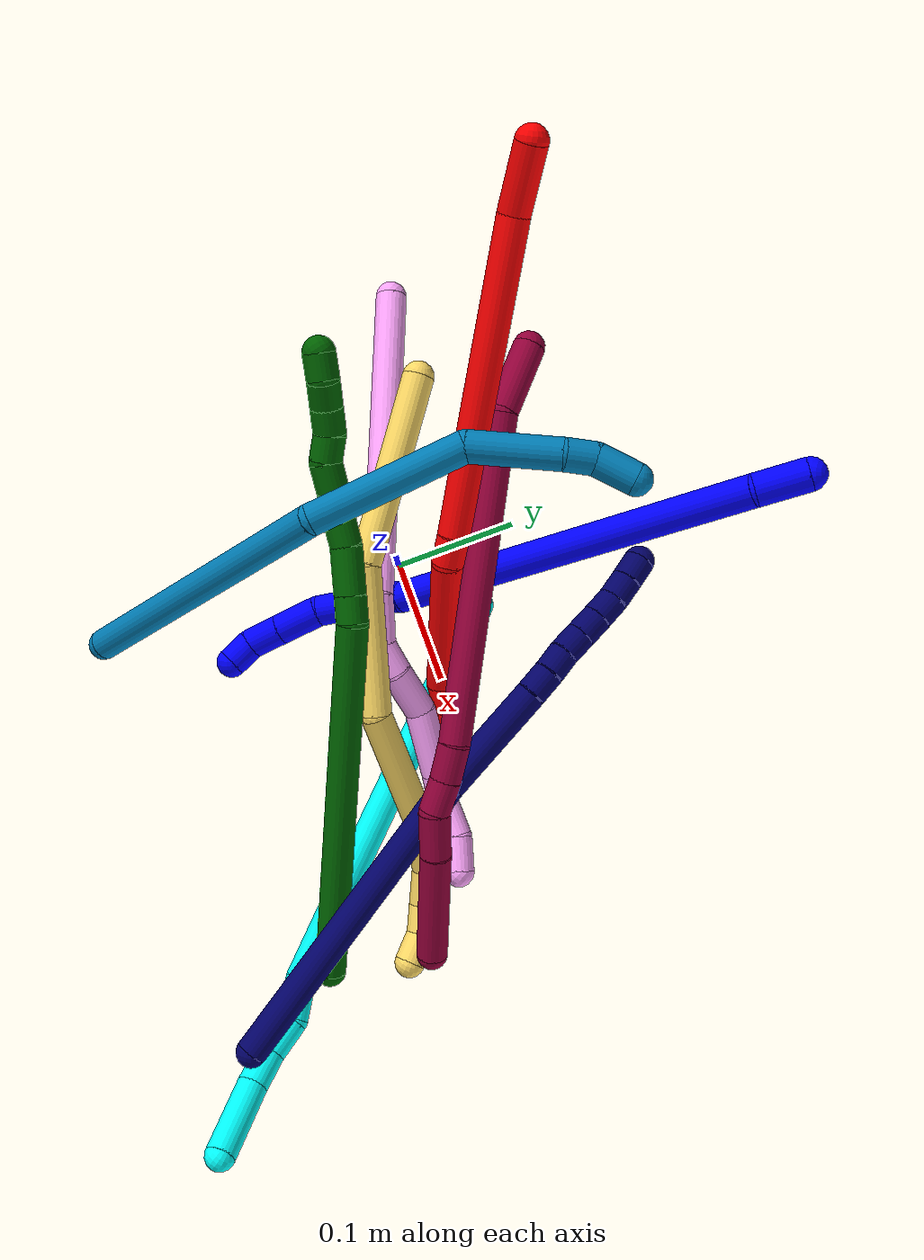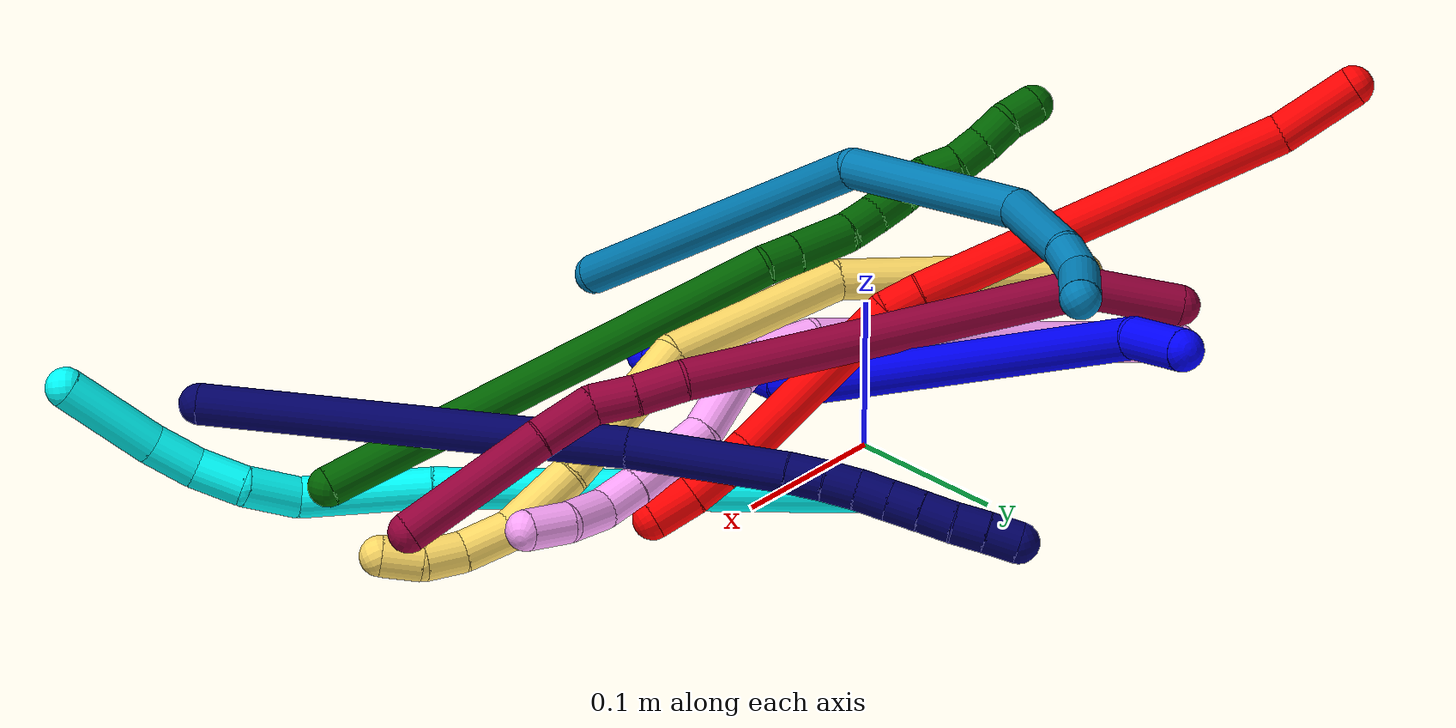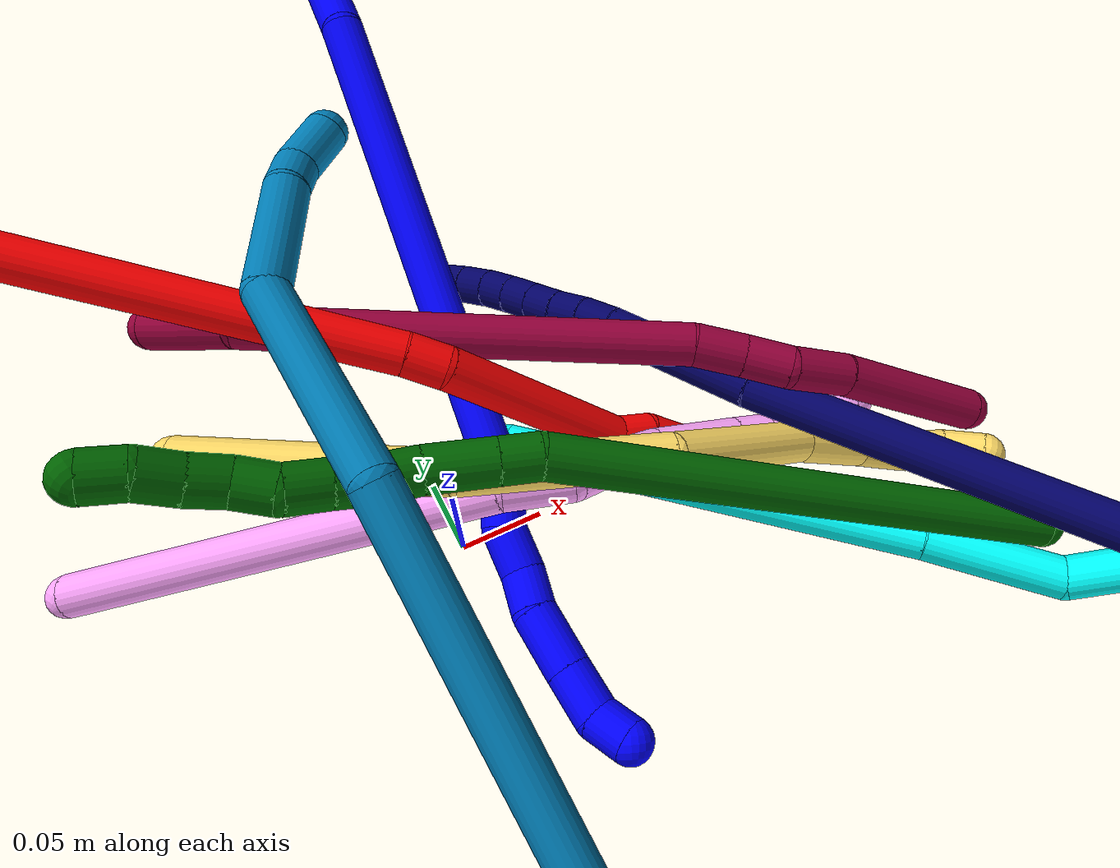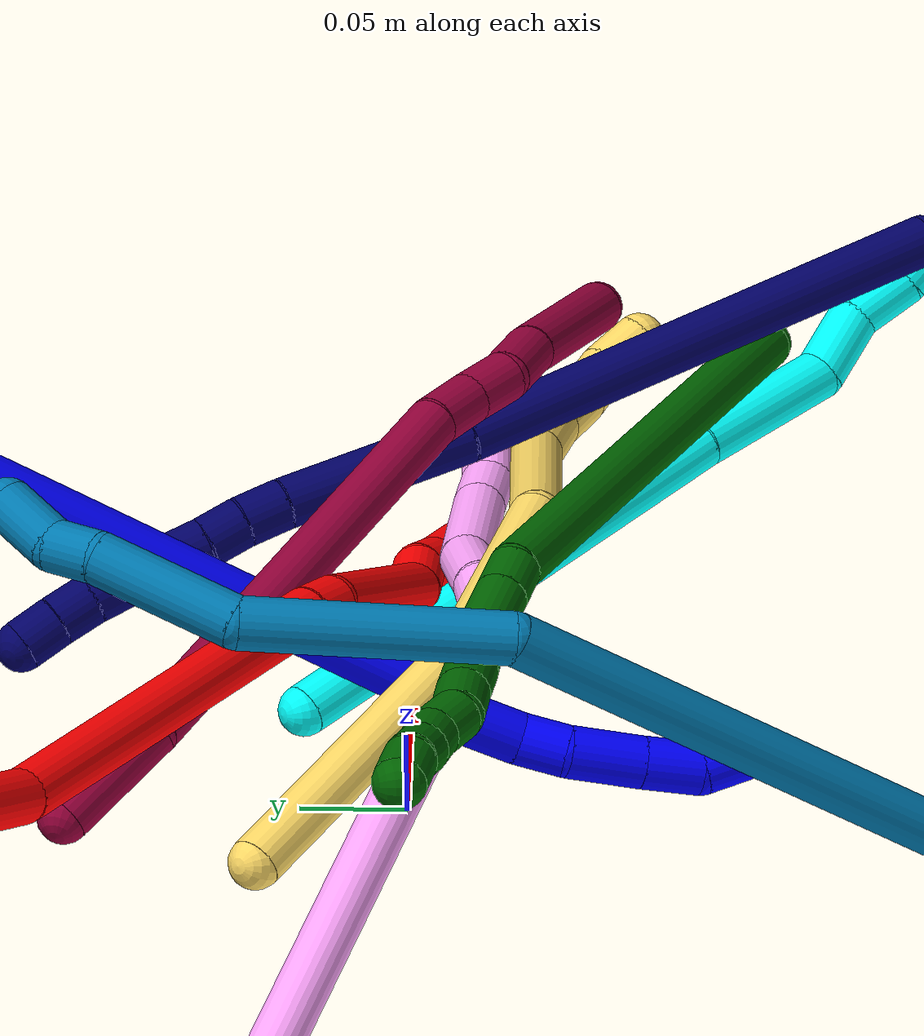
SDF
<sdf version="1.7">
 <world name="default">
  <plugin name="TubeGeneratorPlugin" filename="libtube_generator_plugin.so"/>
  <model name="photoneo_s_sensor">
   <static>1</static>
   <pose>0 0 2 1.57079 1.57079 3.14159</pose>
   <link name="link">
    <inertial><mass>0.1</mass></inertial>
    <sensor name="sensor" type="depth">
     <update_rate>30</update_rate>
     <camera>
      <horizontal_fov>1.22</horizontal_fov>
      <image><width>1920</width><height>1200</height><format>B8G8R8</format></image>
      <clip><near>0.1</near><far>4</far></clip>
      <depth_camera><output>points</output></depth_camera>
     </camera>
     <plugin name="camera_plugin" filename="libgazebo_ros_depth_camera.so">
      <baseline>0.2</baseline>
      <alwaysOn>1</alwaysOn>
      <updateRate>0.0</updateRate>
      <cameraName>camera_ir</cameraName>
      <imageTopicName>/camera/color/image_raw</imageTopicName>
      <cameraInfoTopicName>/camera/color/camera_info</cameraInfoTopicName>
      <depthImageTopicName>/camera/depth/image_raw</depthImageTopicName>
      <depthImageCameraInfoTopicName>/camera/depth/camera_info</depthImageCameraInfoTopicName>
      <pointCloudTopicName>/camera/depth/points</pointCloudTopicName>
      <frameName>fr_optical</frameName>
      <pointCloudCutoff>0.1</pointCloudCutoff>
      <pointCloudCutoffMax>2.0</pointCloudCutoffMax>
      <distortionK1>0</distortionK1>
      <distortionK2>0</distortionK2>
      <distortionK3>0</distortionK3>
      <distortionT1>0</distortionT1>
      <distortionT2>0</distortionT2>
      <CxPrime>0</CxPrime>
      <Cx>0</Cx>
      <Cy>0</Cy>
      <focalLength>0</focalLength>
      <hackBaseline>0</hackBaseline>
     </plugin>
    </sensor>
   </link>
  </model>
  <gravity>0 0 -9.8</gravity>
  <magnetic_field>6e-06 2.3e-05 -4.2e-05</magnetic_field>
  <atmosphere type="adiabatic"/>
  <physics name="default_physics" default="0" type="ode">
   <max_step_size>0.003</max_step_size>
   <real_time_factor>1</real_time_factor>
   <real_time_update_rate>1000</real_time_update_rate>
   <max_contacts>10000</max_contacts>
   <ode>
    <solver>
     <type>quick</type>
     <iters>100</iters>
     <sor>1.3</sor>
     <use_dynamic_moi_rescaling>0</use_dynamic_moi_rescaling>
    </solver>
    <constraints>
     <contact_max_correcting_vel>0</contact_max_correcting_vel>
     <contact_surface_layer>0.001</contact_surface_layer>
     <cfm>0</cfm>
     <erp>0.2</erp>
    </constraints>
   </ode>
  </physics>
  <scene><ambient>0.4 0.4 0.4 1</ambient><background>0.7 0.7 0.7 1</background><shadows>0</shadows></scene>
  <audio><device>default</device></audio>
  <spherical_coordinates>
   <surface_model>EARTH_WGS84</surface_model>
   <latitude_deg>0</latitude_deg>
   <longitude_deg>0</longitude_deg>
   <elevation>0</elevation>
   <heading_deg>0</heading_deg>
  </spherical_coordinates>
  <model name="bin">
   <static>1</static>
   <link name="bottom">
    <collision name="collision-bottom">
     <pose>0 0 -0.01 0 -0 0</pose>
     <geometry><box><size>0.8 0.6 0.02</size></box></geometry>
     <surface>
      <friction><ode><mu>100</mu><mu2>100</mu2></ode></friction>
      <contact><collide_bitmask>65535</collide_bitmask></contact>
     </surface>
    </collision>
   </link>
   <link name="west_wall">
    <collision name="collision-west_wall">
     <pose>-0.41 0 0.1 0 -0 0</pose>
     <geometry><box><size>0.02 0.6 0.2</size></box></geometry>
     <surface>
      <friction><ode><mu>100</mu><mu2>100</mu2></ode></friction>
      <contact><collide_bitmask>65535</collide_bitmask></contact>
     </surface>
    </collision>
   </link>
   <link name="east_wall">
    <collision name="collision-east_wall">
     <pose>0.41 0 0.1 0 -0 0</pose>
     <geometry><box><size>0.02 0.6 0.2</size></box></geometry>
     <surface>
      <friction><ode><mu>100</mu><mu2>100</mu2></ode></friction>
      <contact><collide_bitmask>65535</collide_bitmask></contact>
     </surface>
    </collision>
   </link>
   <link name="south_wall">
    <collision name="collision-south_wall">
     <pose>0 -0.31 0.1 0 -0 0</pose>
     <geometry><box><size>0.8 0.02 0.2</size></box></geometry>
     <surface>
      <friction><ode><mu>100</mu><mu2>100</mu2></ode></friction>
      <contact><collide_bitmask>65535</collide_bitmask></contact>
     </surface>
    </collision>
   </link>
   <link name="north_wall">
    <collision name="collision-north_wall">
     <pose>0 0.31 0.1 0 -0 0</pose>
     <geometry><box><size>0.8 0.02 0.2</size></box></geometry>
     <surface>
      <friction><ode><mu>100</mu><mu2>100</mu2></ode></friction>
      <contact><collide_bitmask>65535</collide_bitmask></contact>
     </surface>
    </collision>
   </link>
  </model>
  <model name="1">
   <static>0</static>
   <link name="1">
    <collision name="collision-cylinder-e_1_1_4">
     <pose>-0.003266 -0.007988 -0.017819 2.72015 -0.165715 -0.740687</pose>
     <geometry><cylinder><radius>0.0125</radius><length>0.039598</length></cylinder></geometry>
     <surface>
      <friction><ode><mu>1.16</mu><mu2>1.16</mu2><slip1>0</slip1><slip2>0</slip2></ode></friction>
      <contact><ode><kp>1e+06</kp><kd>1</kd><max_vel>0</max_vel><min_depth>0.001</min_depth></ode></contact>
     </surface>
    </collision>
    <visual name="visual-cylinder-e_1_1_4">
     <pose>-0.003266 -0.007988 -0.017819 2.72015 -0.165715 -0.740687</pose>
     <geometry><cylinder><radius>0.0125</radius><length>0.039598</length></cylinder></geometry>
     <material><ambient>0 0 1 1</ambient></material>
    </visual>
    <collision name="collision-cylinder-e_2_4_5">
     <pose>0.0062 -0.057261 -0.178897 2.86102 0.085192 0.586255</pose>
     <geometry><cylinder><radius>0.0125</radius><length>0.299262</length></cylinder></geometry>
     <surface>
      <friction><ode><mu>1.16</mu><mu2>1.16</mu2><slip1>0</slip1><slip2>0</slip2></ode></friction>
      <contact><ode><kp>1e+06</kp><kd>1</kd><max_vel>0</max_vel><min_depth>0.001</min_depth></ode></contact>
     </surface>
    </collision>
    <visual name="visual-cylinder-e_2_4_5">
     <pose>0.0062 -0.057261 -0.178897 2.86102 0.085192 0.586255</pose>
     <geometry><cylinder><radius>0.0125</radius><length>0.299262</length></cylinder></geometry>
     <material><ambient>0 0 1 1</ambient></material>
    </visual>
    <collision name="collision-cylinder-e_3_5_6">
     <pose>0.017933 -0.098548 -0.334361 3.14134 -0.08167 -3.13551</pose>
     <geometry><cylinder><radius>0.0125</radius><length>0.024493</length></cylinder></geometry>
     <surface>
      <friction><ode><mu>1.16</mu><mu2>1.16</mu2><slip1>0</slip1><slip2>0</slip2></ode></friction>
      <contact><ode><kp>1e+06</kp><kd>1</kd><max_vel>0</max_vel><min_depth>0.001</min_depth></ode></contact>
     </surface>
    </collision>
    <visual name="visual-cylinder-e_3_5_6">
     <pose>0.017933 -0.098548 -0.334361 3.14134 -0.08167 -3.13551</pose>
     <geometry><cylinder><radius>0.0125</radius><length>0.024493</length></cylinder></geometry>
     <material><ambient>0 0 1 1</ambient></material>
    </visual>
    <collision name="collision-cylinder-e_4_6_7">
     <pose>0.017887 -0.103284 -0.359152 2.78191 0.070742 0.384462</pose>
     <geometry><cylinder><radius>0.0125</radius><length>0.02696</length></cylinder></geometry>
     <surface>
      <friction><ode><mu>1.16</mu><mu2>1.16</mu2><slip1>0</slip1><slip2>0</slip2></ode></friction>
      <contact><ode><kp>1e+06</kp><kd>1</kd><max_vel>0</max_vel><min_depth>0.001</min_depth></ode></contact>
     </surface>
    </collision>
    <visual name="visual-cylinder-e_4_6_7">
     <pose>0.017887 -0.103284 -0.359152 2.78191 0.070742 0.384462</pose>
     <geometry><cylinder><radius>0.0125</radius><length>0.02696</length></cylinder></geometry>
     <material><ambient>0 0 1 1</ambient></material>
    </visual>
    <collision name="collision-cylinder-e_5_7_8">
     <pose>0.015896 -0.111945 -0.38238 2.78798 -0.25387 -1.2405</pose>
     <geometry><cylinder><radius>0.0125</radius><length>0.023439</length></cylinder></geometry>
     <surface>
      <friction><ode><mu>1.16</mu><mu2>1.16</mu2><slip1>0</slip1><slip2>0</slip2></ode></friction>
      <contact><ode><kp>1e+06</kp><kd>1</kd><max_vel>0</max_vel><min_depth>0.001</min_depth></ode></contact>
     </surface>
    </collision>
    <visual name="visual-cylinder-e_5_7_8">
     <pose>0.015896 -0.111945 -0.38238 2.78798 -0.25387 -1.2405</pose>
     <geometry><cylinder><radius>0.0125</radius><length>0.023439</length></cylinder></geometry>
     <material><ambient>0 0 1 1</ambient></material>
    </visual>
    <collision name="collision-cylinder-e_6_8_9">
     <pose>0.011943 -0.125138 -0.408507 2.60241 -0.055922 -0.201749</pose>
     <geometry><cylinder><radius>0.0125</radius><length>0.036146</length></cylinder></geometry>
     <surface>
      <friction><ode><mu>1.16</mu><mu2>1.16</mu2><slip1>0</slip1><slip2>0</slip2></ode></friction>
      <contact><ode><kp>1e+06</kp><kd>1</kd><max_vel>0</max_vel><min_depth>0.001</min_depth></ode></contact>
     </surface>
    </collision>
    <visual name="visual-cylinder-e_6_8_9">
     <pose>0.011943 -0.125138 -0.408507 2.60241 -0.055922 -0.201749</pose>
     <geometry><cylinder><radius>0.0125</radius><length>0.036146</length></cylinder></geometry>
     <material><ambient>0 0 1 1</ambient></material>
    </visual>
    <collision name="collision-cylinder-e_7_9_10">
     <pose>0.009845 -0.141944 -0.435829 2.57435 -0.077313 -0.263836</pose>
     <geometry><cylinder><radius>0.0125</radius><length>0.028154</length></cylinder></geometry>
     <surface>
      <friction><ode><mu>1.16</mu><mu2>1.16</mu2><slip1>0</slip1><slip2>0</slip2></ode></friction>
      <contact><ode><kp>1e+06</kp><kd>1</kd><max_vel>0</max_vel><min_depth>0.001</min_depth></ode></contact>
     </surface>
    </collision>
    <visual name="visual-cylinder-e_7_9_10">
     <pose>0.009845 -0.141944 -0.435829 2.57435 -0.077313 -0.263836</pose>
     <geometry><cylinder><radius>0.0125</radius><length>0.028154</length></cylinder></geometry>
     <material><ambient>0 0 1 1</ambient></material>
    </visual>
    <collision name="collision-cylinder-e_8_10_2">
     <pose>0.007179 -0.158598 -0.453571 2.14573 -0.144414 -0.264561</pose>
     <geometry><cylinder><radius>0.0125</radius><length>0.021947</length></cylinder></geometry>
     <surface>
      <friction><ode><mu>1.16</mu><mu2>1.16</mu2><slip1>0</slip1><slip2>0</slip2></ode></friction>
      <contact><ode><kp>1e+06</kp><kd>1</kd><max_vel>0</max_vel><min_depth>0.001</min_depth></ode></contact>
     </surface>
    </collision>
    <visual name="visual-cylinder-e_8_10_2">
     <pose>0.007179 -0.158598 -0.453571 2.14573 -0.144414 -0.264561</pose>
     <geometry><cylinder><radius>0.0125</radius><length>0.021947</length></cylinder></geometry>
     <material><ambient>0 0 1 1</ambient></material>
    </visual>
    <collision name="collision-sphere-2">
     <pose>0.005599 -0.167712 -0.459476 0 -0 0</pose>
     <geometry><sphere><radius>0.0125</radius></sphere></geometry>
     <surface>
      <friction><ode><mu>1.16</mu><mu2>1.16</mu2><slip1>0</slip1><slip2>0</slip2></ode></friction>
      <contact><ode><kp>1e+06</kp><kd>1</kd><max_vel>0</max_vel><min_depth>0.001</min_depth></ode></contact>
     </surface>
    </collision>
    <visual name="visual-sphere-2">
     <pose>0.005599 -0.167712 -0.459476 0 -0 0</pose>
     <geometry><sphere><radius>0.0125</radius></sphere></geometry>
     <material><ambient>0 0 1 1</ambient></material>
    </visual>
    <collision name="collision-sphere-10">
     <pose>0.008758 -0.149485 -0.447666 0 -0 0</pose>
     <geometry><sphere><radius>0.0125</radius></sphere></geometry>
     <surface>
      <friction><ode><mu>1.16</mu><mu2>1.16</mu2><slip1>0</slip1><slip2>0</slip2></ode></friction>
      <contact><ode><kp>1e+06</kp><kd>1</kd><max_vel>0</max_vel><min_depth>0.001</min_depth></ode></contact>
     </surface>
    </collision>
    <visual name="visual-sphere-10">
     <pose>0.008758 -0.149485 -0.447666 0 -0 0</pose>
     <geometry><sphere><radius>0.0125</radius></sphere></geometry>
     <material><ambient>0 0 1 1</ambient></material>
    </visual>
    <collision name="collision-sphere-9">
     <pose>0.010932 -0.134403 -0.423992 0 -0 0</pose>
     <geometry><sphere><radius>0.0125</radius></sphere></geometry>
     <surface>
      <friction><ode><mu>1.16</mu><mu2>1.16</mu2><slip1>0</slip1><slip2>0</slip2></ode></friction>
      <contact><ode><kp>1e+06</kp><kd>1</kd><max_vel>0</max_vel><min_depth>0.001</min_depth></ode></contact>
     </surface>
    </collision>
    <visual name="visual-sphere-9">
     <pose>0.010932 -0.134403 -0.423992 0 -0 0</pose>
     <geometry><sphere><radius>0.0125</radius></sphere></geometry>
     <material><ambient>0 0 1 1</ambient></material>
    </visual>
    <collision name="collision-sphere-4">
     <pose>-0.006532 -0.015977 -0.035638 0 -0 0</pose>
     <geometry><sphere><radius>0.0125</radius></sphere></geometry>
     <surface>
      <friction><ode><mu>1.16</mu><mu2>1.16</mu2><slip1>0</slip1><slip2>0</slip2></ode></friction>
      <contact><ode><kp>1e+06</kp><kd>1</kd><max_vel>0</max_vel><min_depth>0.001</min_depth></ode></contact>
     </surface>
    </collision>
    <visual name="visual-sphere-4">
     <pose>-0.006532 -0.015977 -0.035638 0 -0 0</pose>
     <geometry><sphere><radius>0.0125</radius></sphere></geometry>
     <material><ambient>0 0 1 1</ambient></material>
    </visual>
    <collision name="collision-sphere-1">
     <geometry><sphere><radius>0.0125</radius></sphere></geometry>
     <surface>
      <friction><ode><mu>1.16</mu><mu2>1.16</mu2><slip1>0</slip1><slip2>0</slip2></ode></friction>
      <contact><ode><kp>1e+06</kp><kd>1</kd><max_vel>0</max_vel><min_depth>0.001</min_depth></ode></contact>
     </surface>
    </collision>
    <visual name="visual-sphere-1">
     <geometry><sphere><radius>0.0125</radius></sphere></geometry>
     <material><ambient>0 0 1 1</ambient></material>
    </visual>
    <collision name="collision-sphere-8">
     <pose>0.012953 -0.115873 -0.393023 0 -0 0</pose>
     <geometry><sphere><radius>0.0125</radius></sphere></geometry>
     <surface>
      <friction><ode><mu>1.16</mu><mu2>1.16</mu2><slip1>0</slip1><slip2>0</slip2></ode></friction>
      <contact><ode><kp>1e+06</kp><kd>1</kd><max_vel>0</max_vel><min_depth>0.001</min_depth></ode></contact>
     </surface>
    </collision>
    <visual name="visual-sphere-8">
     <pose>0.012953 -0.115873 -0.393023 0 -0 0</pose>
     <geometry><sphere><radius>0.0125</radius></sphere></geometry>
     <material><ambient>0 0 1 1</ambient></material>
    </visual>
    <collision name="collision-sphere-5">
     <pose>0.018932 -0.098545 -0.322155 0 -0 0</pose>
     <geometry><sphere><radius>0.0125</radius></sphere></geometry>
     <surface>
      <friction><ode><mu>1.16</mu><mu2>1.16</mu2><slip1>0</slip1><slip2>0</slip2></ode></friction>
      <contact><ode><kp>1e+06</kp><kd>1</kd><max_vel>0</max_vel><min_depth>0.001</min_depth></ode></contact>
     </surface>
    </collision>
    <visual name="visual-sphere-5">
     <pose>0.018932 -0.098545 -0.322155 0 -0 0</pose>
     <geometry><sphere><radius>0.0125</radius></sphere></geometry>
     <material><ambient>0 0 1 1</ambient></material>
    </visual>
    <collision name="collision-sphere-6">
     <pose>0.016934 -0.098551 -0.346566 0 -0 0</pose>
     <geometry><sphere><radius>0.0125</radius></sphere></geometry>
     <surface>
      <friction><ode><mu>1.16</mu><mu2>1.16</mu2><slip1>0</slip1><slip2>0</slip2></ode></friction>
      <contact><ode><kp>1e+06</kp><kd>1</kd><max_vel>0</max_vel><min_depth>0.001</min_depth></ode></contact>
     </surface>
    </collision>
    <visual name="visual-sphere-6">
     <pose>0.016934 -0.098551 -0.346566 0 -0 0</pose>
     <geometry><sphere><radius>0.0125</radius></sphere></geometry>
     <material><ambient>0 0 1 1</ambient></material>
    </visual>
    <collision name="collision-sphere-7">
     <pose>0.01884 -0.108016 -0.371738 0 -0 0</pose>
     <geometry><sphere><radius>0.0125</radius></sphere></geometry>
     <surface>
      <friction><ode><mu>1.16</mu><mu2>1.16</mu2><slip1>0</slip1><slip2>0</slip2></ode></friction>
      <contact><ode><kp>1e+06</kp><kd>1</kd><max_vel>0</max_vel><min_depth>0.001</min_depth></ode></contact>
     </surface>
    </collision>
    <visual name="visual-sphere-7">
     <pose>0.01884 -0.108016 -0.371738 0 -0 0</pose>
     <geometry><sphere><radius>0.0125</radius></sphere></geometry>
     <material><ambient>0 0 1 1</ambient></material>
    </visual>
    <inertial>
     <pose>0.007773 -0.07455 -0.236137 0 -0 0</pose>
     <mass>0.5</mass>
     <inertia>
      <ixx>0.003109</ixx>
      <ixy>0</ixy>
      <ixz>0</ixz>
      <iyy>-0.000563</iyy>
      <iyz>0</iyz>
      <izz>0.000405</izz>
     </inertia>
    </inertial>
   </link>
   <pose>0.054277 0.291635 0.207875 -0.483977 0.953598 0.572842</pose>
  </model>
  <model name="2">
   <static>0</static>
   <link name="2">
    <collision name="collision-cylinder-e_1_1_4">
     <pose>0.001575 0.00493 -0.025423 -2.95006 0.060754 -0.612724</pose>
     <geometry><cylinder><radius>0.0125</radius><length>0.051888</length></cylinder></geometry>
     <surface>
      <friction><ode><mu>1.16</mu><mu2>1.16</mu2><slip1>0</slip1><slip2>0</slip2></ode></friction>
      <contact><ode><kp>1e+06</kp><kd>1</kd><max_vel>0</max_vel><min_depth>0.001</min_depth></ode></contact>
     </surface>
    </collision>
    <visual name="visual-cylinder-e_1_1_4">
     <pose>0.001575 0.00493 -0.025423 -2.95006 0.060754 -0.612724</pose>
     <geometry><cylinder><radius>0.0125</radius><length>0.051888</length></cylinder></geometry>
     <material><ambient>1 0 0 1</ambient></material>
    </visual>
    <collision name="collision-cylinder-e_2_4_5">
     <pose>-0.008923 0.011453 -0.168391 -3.12804 -0.102345 2.87845</pose>
     <geometry><cylinder><radius>0.0125</radius><length>0.23635</length></cylinder></geometry>
     <surface>
      <friction><ode><mu>1.16</mu><mu2>1.16</mu2><slip1>0</slip1><slip2>0</slip2></ode></friction>
      <contact><ode><kp>1e+06</kp><kd>1</kd><max_vel>0</max_vel><min_depth>0.001</min_depth></ode></contact>
     </surface>
    </collision>
    <visual name="visual-cylinder-e_2_4_5">
     <pose>-0.008923 0.011453 -0.168391 -3.12804 -0.102345 2.87845</pose>
     <geometry><cylinder><radius>0.0125</radius><length>0.23635</length></cylinder></geometry>
     <material><ambient>1 0 0 1</ambient></material>
    </visual>
    <collision name="collision-cylinder-e_3_5_6">
     <pose>-0.021373 0.014119 -0.297284 -3.04737 -0.033042 0.67415</pose>
     <geometry><cylinder><radius>0.0125</radius><length>0.022807</length></cylinder></geometry>
     <surface>
      <friction><ode><mu>1.16</mu><mu2>1.16</mu2><slip1>0</slip1><slip2>0</slip2></ode></friction>
      <contact><ode><kp>1e+06</kp><kd>1</kd><max_vel>0</max_vel><min_depth>0.001</min_depth></ode></contact>
     </surface>
    </collision>
    <visual name="visual-cylinder-e_3_5_6">
     <pose>-0.021373 0.014119 -0.297284 -3.04737 -0.033042 0.67415</pose>
     <geometry><cylinder><radius>0.0125</radius><length>0.022807</length></cylinder></geometry>
     <material><ambient>1 0 0 1</ambient></material>
    </visual>
    <collision name="collision-cylinder-e_4_6_7">
     <pose>-0.006941 0.022004 -0.364514 -3.02028 0.257228 -2.26357</pose>
     <geometry><cylinder><radius>0.0125</radius><length>0.116425</length></cylinder></geometry>
     <surface>
      <friction><ode><mu>1.16</mu><mu2>1.16</mu2><slip1>0</slip1><slip2>0</slip2></ode></friction>
      <contact><ode><kp>1e+06</kp><kd>1</kd><max_vel>0</max_vel><min_depth>0.001</min_depth></ode></contact>
     </surface>
    </collision>
    <visual name="visual-cylinder-e_4_6_7">
     <pose>-0.006941 0.022004 -0.364514 -3.02028 0.257228 -2.26357</pose>
     <geometry><cylinder><radius>0.0125</radius><length>0.116425</length></cylinder></geometry>
     <material><ambient>1 0 0 1</ambient></material>
    </visual>
    <collision name="collision-cylinder-e_5_7_8">
     <pose>0.010179 0.025332 -0.431047 2.8254 0.20332 1.13843</pose>
     <geometry><cylinder><radius>0.0125</radius><length>0.022881</length></cylinder></geometry>
     <surface>
      <friction><ode><mu>1.16</mu><mu2>1.16</mu2><slip1>0</slip1><slip2>0</slip2></ode></friction>
      <contact><ode><kp>1e+06</kp><kd>1</kd><max_vel>0</max_vel><min_depth>0.001</min_depth></ode></contact>
     </surface>
    </collision>
    <visual name="visual-cylinder-e_5_7_8">
     <pose>0.010179 0.025332 -0.431047 2.8254 0.20332 1.13843</pose>
     <geometry><cylinder><radius>0.0125</radius><length>0.022881</length></cylinder></geometry>
     <material><ambient>1 0 0 1</ambient></material>
    </visual>
    <collision name="collision-cylinder-e_6_8_9">
     <pose>0.014208 0.022586 -0.452225 -3.0716 0.161458 -2.32478</pose>
     <geometry><cylinder><radius>0.0125</radius><length>0.021388</length></cylinder></geometry>
     <surface>
      <friction><ode><mu>1.16</mu><mu2>1.16</mu2><slip1>0</slip1><slip2>0</slip2></ode></friction>
      <contact><ode><kp>1e+06</kp><kd>1</kd><max_vel>0</max_vel><min_depth>0.001</min_depth></ode></contact>
     </surface>
    </collision>
    <visual name="visual-cylinder-e_6_8_9">
     <pose>0.014208 0.022586 -0.452225 -3.0716 0.161458 -2.32478</pose>
     <geometry><cylinder><radius>0.0125</radius><length>0.021388</length></cylinder></geometry>
     <material><ambient>1 0 0 1</ambient></material>
    </visual>
    <collision name="collision-cylinder-e_7_9_2">
     <pose>0.016367 0.023273 -0.476878 3.13794 0.031109 2.90801</pose>
     <geometry><cylinder><radius>0.0125</radius><length>0.028261</length></cylinder></geometry>
     <surface>
      <friction><ode><mu>1.16</mu><mu2>1.16</mu2><slip1>0</slip1><slip2>0</slip2></ode></friction>
      <contact><ode><kp>1e+06</kp><kd>1</kd><max_vel>0</max_vel><min_depth>0.001</min_depth></ode></contact>
     </surface>
    </collision>
    <visual name="visual-cylinder-e_7_9_2">
     <pose>0.016367 0.023273 -0.476878 3.13794 0.031109 2.90801</pose>
     <geometry><cylinder><radius>0.0125</radius><length>0.028261</length></cylinder></geometry>
     <material><ambient>1 0 0 1</ambient></material>
    </visual>
    <collision name="collision-sphere-2">
     <pose>0.016806 0.023221 -0.491001 0 -0 0</pose>
     <geometry><sphere><radius>0.0125</radius></sphere></geometry>
     <surface>
      <friction><ode><mu>1.16</mu><mu2>1.16</mu2><slip1>0</slip1><slip2>0</slip2></ode></friction>
      <contact><ode><kp>1e+06</kp><kd>1</kd><max_vel>0</max_vel><min_depth>0.001</min_depth></ode></contact>
     </surface>
    </collision>
    <visual name="visual-sphere-2">
     <pose>0.016806 0.023221 -0.491001 0 -0 0</pose>
     <geometry><sphere><radius>0.0125</radius></sphere></geometry>
     <material><ambient>1 0 0 1</ambient></material>
    </visual>
    <collision name="collision-sphere-9">
     <pose>0.015927 0.023325 -0.462754 0 -0 0</pose>
     <geometry><sphere><radius>0.0125</radius></sphere></geometry>
     <surface>
      <friction><ode><mu>1.16</mu><mu2>1.16</mu2><slip1>0</slip1><slip2>0</slip2></ode></friction>
      <contact><ode><kp>1e+06</kp><kd>1</kd><max_vel>0</max_vel><min_depth>0.001</min_depth></ode></contact>
     </surface>
    </collision>
    <visual name="visual-sphere-9">
     <pose>0.015927 0.023325 -0.462754 0 -0 0</pose>
     <geometry><sphere><radius>0.0125</radius></sphere></geometry>
     <material><ambient>1 0 0 1</ambient></material>
    </visual>
    <collision name="collision-sphere-4">
     <pose>0.00315 0.009859 -0.050845 0 -0 0</pose>
     <geometry><sphere><radius>0.0125</radius></sphere></geometry>
     <surface>
      <friction><ode><mu>1.16</mu><mu2>1.16</mu2><slip1>0</slip1><slip2>0</slip2></ode></friction>
      <contact><ode><kp>1e+06</kp><kd>1</kd><max_vel>0</max_vel><min_depth>0.001</min_depth></ode></contact>
     </surface>
    </collision>
    <visual name="visual-sphere-4">
     <pose>0.00315 0.009859 -0.050845 0 -0 0</pose>
     <geometry><sphere><radius>0.0125</radius></sphere></geometry>
     <material><ambient>1 0 0 1</ambient></material>
    </visual>
    <collision name="collision-sphere-1">
     <geometry><sphere><radius>0.0125</radius></sphere></geometry>
     <surface>
      <friction><ode><mu>1.16</mu><mu2>1.16</mu2><slip1>0</slip1><slip2>0</slip2></ode></friction>
      <contact><ode><kp>1e+06</kp><kd>1</kd><max_vel>0</max_vel><min_depth>0.001</min_depth></ode></contact>
     </surface>
    </collision>
    <visual name="visual-sphere-1">
     <geometry><sphere><radius>0.0125</radius></sphere></geometry>
     <material><ambient>1 0 0 1</ambient></material>
    </visual>
    <collision name="collision-sphere-8">
     <pose>0.012489 0.021848 -0.441696 0 -0 0</pose>
     <geometry><sphere><radius>0.0125</radius></sphere></geometry>
     <surface>
      <friction><ode><mu>1.16</mu><mu2>1.16</mu2><slip1>0</slip1><slip2>0</slip2></ode></friction>
      <contact><ode><kp>1e+06</kp><kd>1</kd><max_vel>0</max_vel><min_depth>0.001</min_depth></ode></contact>
     </surface>
    </collision>
    <visual name="visual-sphere-8">
     <pose>0.012489 0.021848 -0.441696 0 -0 0</pose>
     <geometry><sphere><radius>0.0125</radius></sphere></geometry>
     <material><ambient>1 0 0 1</ambient></material>
    </visual>
    <collision name="collision-sphere-5">
     <pose>-0.020997 0.013047 -0.285937 0 -0 0</pose>
     <geometry><sphere><radius>0.0125</radius></sphere></geometry>
     <surface>
      <friction><ode><mu>1.16</mu><mu2>1.16</mu2><slip1>0</slip1><slip2>0</slip2></ode></friction>
      <contact><ode><kp>1e+06</kp><kd>1</kd><max_vel>0</max_vel><min_depth>0.001</min_depth></ode></contact>
     </surface>
    </collision>
    <visual name="visual-sphere-5">
     <pose>-0.020997 0.013047 -0.285937 0 -0 0</pose>
     <geometry><sphere><radius>0.0125</radius></sphere></geometry>
     <material><ambient>1 0 0 1</ambient></material>
    </visual>
    <collision name="collision-sphere-6">
     <pose>-0.02175 0.015191 -0.30863 0 -0 0</pose>
     <geometry><sphere><radius>0.0125</radius></sphere></geometry>
     <surface>
      <friction><ode><mu>1.16</mu><mu2>1.16</mu2><slip1>0</slip1><slip2>0</slip2></ode></friction>
      <contact><ode><kp>1e+06</kp><kd>1</kd><max_vel>0</max_vel><min_depth>0.001</min_depth></ode></contact>
     </surface>
    </collision>
    <visual name="visual-sphere-6">
     <pose>-0.02175 0.015191 -0.30863 0 -0 0</pose>
     <geometry><sphere><radius>0.0125</radius></sphere></geometry>
     <material><ambient>1 0 0 1</ambient></material>
    </visual>
    <collision name="collision-sphere-7">
     <pose>0.007869 0.028816 -0.420398 0 -0 0</pose>
     <geometry><sphere><radius>0.0125</radius></sphere></geometry>
     <surface>
      <friction><ode><mu>1.16</mu><mu2>1.16</mu2><slip1>0</slip1><slip2>0</slip2></ode></friction>
      <contact><ode><kp>1e+06</kp><kd>1</kd><max_vel>0</max_vel><min_depth>0.001</min_depth></ode></contact>
     </surface>
    </collision>
    <visual name="visual-sphere-7">
     <pose>0.007869 0.028816 -0.420398 0 -0 0</pose>
     <geometry><sphere><radius>0.0125</radius></sphere></geometry>
     <material><ambient>1 0 0 1</ambient></material>
    </visual>
    <inertial>
     <pose>-0.004647 0.015134 -0.246698 0 -0 0</pose>
     <mass>0.5</mass>
     <inertia><ixx>-0.000959</ixx><ixy>0</ixy><ixz>0</ixz><iyy>0.001334</iyy><iyz>0</iyz><izz>6e-06</izz></inertia>
    </inertial>
   </link>
   <pose>-0.226764 0.185387 0.227986 -0.951174 0.840828 1.59629</pose>
  </model>
  <model name="3">
   <static>0</static>
   <link name="3">
    <collision name="collision-cylinder-e_1_1_4">
     <pose>0.023661 -0.029963 0.123814 0.237435 0.183646 0.021966</pose>
     <geometry><cylinder><radius>0.0125</radius><length>0.259132</length></cylinder></geometry>
     <surface>
      <friction><ode><mu>1.16</mu><mu2>1.16</mu2><slip1>0</slip1><slip2>0</slip2></ode></friction>
      <contact><ode><kp>1e+06</kp><kd>1</kd><max_vel>0</max_vel><min_depth>0.001</min_depth></ode></contact>
     </surface>
    </collision>
    <visual name="visual-cylinder-e_1_1_4">
     <pose>0.023661 -0.029963 0.123814 0.237435 0.183646 0.021966</pose>
     <geometry><cylinder><radius>0.0125</radius><length>0.259132</length></cylinder></geometry>
     <material><ambient>0.003922 1 0.996078 1</ambient></material>
    </visual>
    <collision name="collision-cylinder-e_2_4_5">
     <pose>0.050976 -0.068642 0.286911 0.21834 0.090564 0.009933</pose>
     <geometry><cylinder><radius>0.0125</radius><length>0.08081</length></cylinder></geometry>
     <surface>
      <friction><ode><mu>1.16</mu><mu2>1.16</mu2><slip1>0</slip1><slip2>0</slip2></ode></friction>
      <contact><ode><kp>1e+06</kp><kd>1</kd><max_vel>0</max_vel><min_depth>0.001</min_depth></ode></contact>
     </surface>
    </collision>
    <visual name="visual-cylinder-e_2_4_5">
     <pose>0.050976 -0.068642 0.286911 0.21834 0.090564 0.009933</pose>
     <geometry><cylinder><radius>0.0125</radius><length>0.08081</length></cylinder></geometry>
     <material><ambient>0.003922 1 0.996078 1</ambient></material>
    </visual>
    <collision name="collision-cylinder-e_3_5_6">
     <pose>0.062478 -0.086464 0.339445 0.602144 0.454124 0.14324</pose>
     <geometry><cylinder><radius>0.0125</radius><length>0.035781</length></cylinder></geometry>
     <surface>
      <friction><ode><mu>1.16</mu><mu2>1.16</mu2><slip1>0</slip1><slip2>0</slip2></ode></friction>
      <contact><ode><kp>1e+06</kp><kd>1</kd><max_vel>0</max_vel><min_depth>0.001</min_depth></ode></contact>
     </surface>
    </collision>
    <visual name="visual-cylinder-e_3_5_6">
     <pose>0.062478 -0.086464 0.339445 0.602144 0.454124 0.14324</pose>
     <geometry><cylinder><radius>0.0125</radius><length>0.035781</length></cylinder></geometry>
     <material><ambient>0.003922 1 0.996078 1</ambient></material>
    </visual>
    <collision name="collision-cylinder-e_4_6_7">
     <pose>0.077971 -0.097299 0.365917 0.129937 0.520536 0.034649</pose>
     <geometry><cylinder><radius>0.0125</radius><length>0.030741</length></cylinder></geometry>
     <surface>
      <friction><ode><mu>1.16</mu><mu2>1.16</mu2><slip1>0</slip1><slip2>0</slip2></ode></friction>
      <contact><ode><kp>1e+06</kp><kd>1</kd><max_vel>0</max_vel><min_depth>0.001</min_depth></ode></contact>
     </surface>
    </collision>
    <visual name="visual-cylinder-e_4_6_7">
     <pose>0.077971 -0.097299 0.365917 0.129937 0.520536 0.034649</pose>
     <geometry><cylinder><radius>0.0125</radius><length>0.030741</length></cylinder></geometry>
     <material><ambient>0.003922 1 0.996078 1</ambient></material>
    </visual>
    <collision name="collision-cylinder-e_5_7_8">
     <pose>0.095528 -0.103084 0.390062 0.355693 0.704928 0.132037</pose>
     <geometry><cylinder><radius>0.0125</radius><length>0.030596</length></cylinder></geometry>
     <surface>
      <friction><ode><mu>1.16</mu><mu2>1.16</mu2><slip1>0</slip1><slip2>0</slip2></ode></friction>
      <contact><ode><kp>1e+06</kp><kd>1</kd><max_vel>0</max_vel><min_depth>0.001</min_depth></ode></contact>
     </surface>
    </collision>
    <visual name="visual-cylinder-e_5_7_8">
     <pose>0.095528 -0.103084 0.390062 0.355693 0.704928 0.132037</pose>
     <geometry><cylinder><radius>0.0125</radius><length>0.030596</length></cylinder></geometry>
     <material><ambient>0.003922 1 0.996078 1</ambient></material>
    </visual>
    <collision name="collision-cylinder-e_6_8_2">
     <pose>0.12808 -0.117438 0.420266 0.490479 0.802913 0.211697</pose>
     <geometry><cylinder><radius>0.0125</radius><length>0.06294</length></cylinder></geometry>
     <surface>
      <friction><ode><mu>1.16</mu><mu2>1.16</mu2><slip1>0</slip1><slip2>0</slip2></ode></friction>
      <contact><ode><kp>1e+06</kp><kd>1</kd><max_vel>0</max_vel><min_depth>0.001</min_depth></ode></contact>
     </surface>
    </collision>
    <visual name="visual-cylinder-e_6_8_2">
     <pose>0.12808 -0.117438 0.420266 0.490479 0.802913 0.211697</pose>
     <geometry><cylinder><radius>0.0125</radius><length>0.06294</length></cylinder></geometry>
     <material><ambient>0.003922 1 0.996078 1</ambient></material>
    </visual>
    <collision name="collision-sphere-2">
     <pose>0.150718 -0.127735 0.439549 0 -0 0</pose>
     <geometry><sphere><radius>0.0125</radius></sphere></geometry>
     <surface>
      <friction><ode><mu>1.16</mu><mu2>1.16</mu2><slip1>0</slip1><slip2>0</slip2></ode></friction>
      <contact><ode><kp>1e+06</kp><kd>1</kd><max_vel>0</max_vel><min_depth>0.001</min_depth></ode></contact>
     </surface>
    </collision>
    <visual name="visual-sphere-2">
     <pose>0.150718 -0.127735 0.439549 0 -0 0</pose>
     <geometry><sphere><radius>0.0125</radius></sphere></geometry>
     <material><ambient>0.003922 1 0.996078 1</ambient></material>
    </visual>
    <collision name="collision-sphere-4">
     <pose>0.047321 -0.059926 0.247627 0 -0 0</pose>
     <geometry><sphere><radius>0.0125</radius></sphere></geometry>
     <surface>
      <friction><ode><mu>1.16</mu><mu2>1.16</mu2><slip1>0</slip1><slip2>0</slip2></ode></friction>
      <contact><ode><kp>1e+06</kp><kd>1</kd><max_vel>0</max_vel><min_depth>0.001</min_depth></ode></contact>
     </surface>
    </collision>
    <visual name="visual-sphere-4">
     <pose>0.047321 -0.059926 0.247627 0 -0 0</pose>
     <geometry><sphere><radius>0.0125</radius></sphere></geometry>
     <material><ambient>0.003922 1 0.996078 1</ambient></material>
    </visual>
    <collision name="collision-sphere-1">
     <geometry><sphere><radius>0.0125</radius></sphere></geometry>
     <surface>
      <friction><ode><mu>1.16</mu><mu2>1.16</mu2><slip1>0</slip1><slip2>0</slip2></ode></friction>
      <contact><ode><kp>1e+06</kp><kd>1</kd><max_vel>0</max_vel><min_depth>0.001</min_depth></ode></contact>
     </surface>
    </collision>
    <visual name="visual-sphere-1">
     <geometry><sphere><radius>0.0125</radius></sphere></geometry>
     <material><ambient>0.003922 1 0.996078 1</ambient></material>
    </visual>
    <collision name="collision-sphere-8">
     <pose>0.105441 -0.107142 0.400984 0 -0 0</pose>
     <geometry><sphere><radius>0.0125</radius></sphere></geometry>
     <surface>
      <friction><ode><mu>1.16</mu><mu2>1.16</mu2><slip1>0</slip1><slip2>0</slip2></ode></friction>
      <contact><ode><kp>1e+06</kp><kd>1</kd><max_vel>0</max_vel><min_depth>0.001</min_depth></ode></contact>
     </surface>
    </collision>
    <visual name="visual-sphere-8">
     <pose>0.105441 -0.107142 0.400984 0 -0 0</pose>
     <geometry><sphere><radius>0.0125</radius></sphere></geometry>
     <material><ambient>0.003922 1 0.996078 1</ambient></material>
    </visual>
    <collision name="collision-sphere-5">
     <pose>0.05463 -0.077358 0.326195 0 -0 0</pose>
     <geometry><sphere><radius>0.0125</radius></sphere></geometry>
     <surface>
      <friction><ode><mu>1.16</mu><mu2>1.16</mu2><slip1>0</slip1><slip2>0</slip2></ode></friction>
      <contact><ode><kp>1e+06</kp><kd>1</kd><max_vel>0</max_vel><min_depth>0.001</min_depth></ode></contact>
     </surface>
    </collision>
    <visual name="visual-sphere-5">
     <pose>0.05463 -0.077358 0.326195 0 -0 0</pose>
     <geometry><sphere><radius>0.0125</radius></sphere></geometry>
     <material><ambient>0.003922 1 0.996078 1</ambient></material>
    </visual>
    <collision name="collision-sphere-6">
     <pose>0.070326 -0.095571 0.352694 0 -0 0</pose>
     <geometry><sphere><radius>0.0125</radius></sphere></geometry>
     <surface>
      <friction><ode><mu>1.16</mu><mu2>1.16</mu2><slip1>0</slip1><slip2>0</slip2></ode></friction>
      <contact><ode><kp>1e+06</kp><kd>1</kd><max_vel>0</max_vel><min_depth>0.001</min_depth></ode></contact>
     </surface>
    </collision>
    <visual name="visual-sphere-6">
     <pose>0.070326 -0.095571 0.352694 0 -0 0</pose>
     <geometry><sphere><radius>0.0125</radius></sphere></geometry>
     <material><ambient>0.003922 1 0.996078 1</ambient></material>
    </visual>
    <collision name="collision-sphere-7">
     <pose>0.085615 -0.099026 0.379139 0 -0 0</pose>
     <geometry><sphere><radius>0.0125</radius></sphere></geometry>
     <surface>
      <friction><ode><mu>1.16</mu><mu2>1.16</mu2><slip1>0</slip1><slip2>0</slip2></ode></friction>
      <contact><ode><kp>1e+06</kp><kd>1</kd><max_vel>0</max_vel><min_depth>0.001</min_depth></ode></contact>
     </surface>
    </collision>
    <visual name="visual-sphere-7">
     <pose>0.085615 -0.099026 0.379139 0 -0 0</pose>
     <geometry><sphere><radius>0.0125</radius></sphere></geometry>
     <material><ambient>0.003922 1 0.996078 1</ambient></material>
    </visual>
    <inertial>
     <pose>0.051734 -0.059883 0.234099 0 -0 0</pose>
     <mass>0.5</mass>
     <inertia><ixx>0.001557</ixx><ixy>0</ixy><ixz>0</ixz><iyy>0.001526</iyy><iyz>0</iyz><izz>0.0001</izz></inertia>
    </inertial>
   </link>
   <pose>0.053652 0.049905 0.011507 -2.32023 -1.25286 -1.82731</pose>
  </model>
  <model name="4">
   <static>0</static>
   <link name="4">
    <collision name="collision-cylinder-e_1_1_4">
     <pose>0.079052 -0.067173 0.075465 0.727329 0.663949 0.260915</pose>
     <geometry><cylinder><radius>0.0125</radius><length>0.256566</length></cylinder></geometry>
     <surface>
      <friction><ode><mu>1.16</mu><mu2>1.16</mu2><slip1>0</slip1><slip2>0</slip2></ode></friction>
      <contact><ode><kp>1e+06</kp><kd>1</kd><max_vel>0</max_vel><min_depth>0.001</min_depth></ode></contact>
     </surface>
    </collision>
    <visual name="visual-cylinder-e_1_1_4">
     <pose>0.079052 -0.067173 0.075465 0.727329 0.663949 0.260915</pose>
     <geometry><cylinder><radius>0.0125</radius><length>0.256566</length></cylinder></geometry>
     <material><ambient>1 0.65098 0.996078 1</ambient></material>
    </visual>
    <collision name="collision-cylinder-e_2_4_5">
     <pose>0.17161 -0.139218 0.164559 0.343323 0.750873 0.136447</pose>
     <geometry><cylinder><radius>0.0125</radius><length>0.039591</length></cylinder></geometry>
     <surface>
      <friction><ode><mu>1.16</mu><mu2>1.16</mu2><slip1>0</slip1><slip2>0</slip2></ode></friction>
      <contact><ode><kp>1e+06</kp><kd>1</kd><max_vel>0</max_vel><min_depth>0.001</min_depth></ode></contact>
     </surface>
    </collision>
    <visual name="visual-cylinder-e_2_4_5">
     <pose>0.17161 -0.139218 0.164559 0.343323 0.750873 0.136447</pose>
     <geometry><cylinder><radius>0.0125</radius><length>0.039591</length></cylinder></geometry>
     <material><ambient>1 0.65098 0.996078 1</ambient></material>
    </visual>
    <collision name="collision-cylinder-e_3_5_6">
     <pose>0.189829 -0.143136 0.18993 -0.081044 0.380511 -0.015616</pose>
     <geometry><cylinder><radius>0.0125</radius><length>0.025379</length></cylinder></geometry>
     <surface>
      <friction><ode><mu>1.16</mu><mu2>1.16</mu2><slip1>0</slip1><slip2>0</slip2></ode></friction>
      <contact><ode><kp>1e+06</kp><kd>1</kd><max_vel>0</max_vel><min_depth>0.001</min_depth></ode></contact>
     </surface>
    </collision>
    <visual name="visual-cylinder-e_3_5_6">
     <pose>0.189829 -0.143136 0.18993 -0.081044 0.380511 -0.015616</pose>
     <geometry><cylinder><radius>0.0125</radius><length>0.025379</length></cylinder></geometry>
     <material><ambient>1 0.65098 0.996078 1</ambient></material>
    </visual>
    <collision name="collision-cylinder-e_4_6_7">
     <pose>0.202052 -0.137038 0.218936 -0.289593 0.39503 -0.058346</pose>
     <geometry><cylinder><radius>0.0125</radius><length>0.039032</length></cylinder></geometry>
     <surface>
      <friction><ode><mu>1.16</mu><mu2>1.16</mu2><slip1>0</slip1><slip2>0</slip2></ode></friction>
      <contact><ode><kp>1e+06</kp><kd>1</kd><max_vel>0</max_vel><min_depth>0.001</min_depth></ode></contact>
     </surface>
    </collision>
    <visual name="visual-cylinder-e_4_6_7">
     <pose>0.202052 -0.137038 0.218936 -0.289593 0.39503 -0.058346</pose>
     <geometry><cylinder><radius>0.0125</radius><length>0.039032</length></cylinder></geometry>
     <material><ambient>1 0.65098 0.996078 1</ambient></material>
    </visual>
    <collision name="collision-cylinder-e_5_7_8">
     <pose>0.226168 -0.130706 0.258539 -0.053152 0.638524 -0.017574</pose>
     <geometry><cylinder><radius>0.0125</radius><length>0.05572</length></cylinder></geometry>
     <surface>
      <friction><ode><mu>1.16</mu><mu2>1.16</mu2><slip1>0</slip1><slip2>0</slip2></ode></friction>
      <contact><ode><kp>1e+06</kp><kd>1</kd><max_vel>0</max_vel><min_depth>0.001</min_depth></ode></contact>
     </surface>
    </collision>
    <visual name="visual-cylinder-e_5_7_8">
     <pose>0.226168 -0.130706 0.258539 -0.053152 0.638524 -0.017574</pose>
     <geometry><cylinder><radius>0.0125</radius><length>0.05572</length></cylinder></geometry>
     <material><ambient>1 0.65098 0.996078 1</ambient></material>
    </visual>
    <collision name="collision-cylinder-e_6_8_9">
     <pose>0.250729 -0.129599 0.290788 0.00821 0.676444 0.002888</pose>
     <geometry><cylinder><radius>0.0125</radius><length>0.025417</length></cylinder></geometry>
     <surface>
      <friction><ode><mu>1.16</mu><mu2>1.16</mu2><slip1>0</slip1><slip2>0</slip2></ode></friction>
      <contact><ode><kp>1e+06</kp><kd>1</kd><max_vel>0</max_vel><min_depth>0.001</min_depth></ode></contact>
     </surface>
    </collision>
    <visual name="visual-cylinder-e_6_8_9">
     <pose>0.250729 -0.129599 0.290788 0.00821 0.676444 0.002888</pose>
     <geometry><cylinder><radius>0.0125</radius><length>0.025417</length></cylinder></geometry>
     <material><ambient>1 0.65098 0.996078 1</ambient></material>
    </visual>
    <collision name="collision-cylinder-e_7_9_10">
     <pose>0.264315 -0.134815 0.313702 0.376044 0.382819 0.073708</pose>
     <geometry><cylinder><radius>0.0125</radius><length>0.030145</length></cylinder></geometry>
     <surface>
      <friction><ode><mu>1.16</mu><mu2>1.16</mu2><slip1>0</slip1><slip2>0</slip2></ode></friction>
      <contact><ode><kp>1e+06</kp><kd>1</kd><max_vel>0</max_vel><min_depth>0.001</min_depth></ode></contact>
     </surface>
    </collision>
    <visual name="visual-cylinder-e_7_9_10">
     <pose>0.264315 -0.134815 0.313702 0.376044 0.382819 0.073708</pose>
     <geometry><cylinder><radius>0.0125</radius><length>0.030145</length></cylinder></geometry>
     <material><ambient>1 0.65098 0.996078 1</ambient></material>
    </visual>
    <collision name="collision-cylinder-e_8_10_2">
     <pose>0.278635 -0.145416 0.336335 0.516364 0.665489 0.182022</pose>
     <geometry><cylinder><radius>0.0125</radius><length>0.028149</length></cylinder></geometry>
     <surface>
      <friction><ode><mu>1.16</mu><mu2>1.16</mu2><slip1>0</slip1><slip2>0</slip2></ode></friction>
      <contact><ode><kp>1e+06</kp><kd>1</kd><max_vel>0</max_vel><min_depth>0.001</min_depth></ode></contact>
     </surface>
    </collision>
    <visual name="visual-cylinder-e_8_10_2">
     <pose>0.278635 -0.145416 0.336335 0.516364 0.665489 0.182022</pose>
     <geometry><cylinder><radius>0.0125</radius><length>0.028149</length></cylinder></geometry>
     <material><ambient>1 0.65098 0.996078 1</ambient></material>
    </visual>
    <collision name="collision-sphere-2">
     <pose>0.287325 -0.150882 0.345962 0 -0 0</pose>
     <geometry><sphere><radius>0.0125</radius></sphere></geometry>
     <surface>
      <friction><ode><mu>1.16</mu><mu2>1.16</mu2><slip1>0</slip1><slip2>0</slip2></ode></friction>
      <contact><ode><kp>1e+06</kp><kd>1</kd><max_vel>0</max_vel><min_depth>0.001</min_depth></ode></contact>
     </surface>
    </collision>
    <visual name="visual-sphere-2">
     <pose>0.287325 -0.150882 0.345962 0 -0 0</pose>
     <geometry><sphere><radius>0.0125</radius></sphere></geometry>
     <material><ambient>1 0.65098 0.996078 1</ambient></material>
    </visual>
    <collision name="collision-sphere-10">
     <pose>0.269945 -0.13995 0.326707 0 -0 0</pose>
     <geometry><sphere><radius>0.0125</radius></sphere></geometry>
     <surface>
      <friction><ode><mu>1.16</mu><mu2>1.16</mu2><slip1>0</slip1><slip2>0</slip2></ode></friction>
      <contact><ode><kp>1e+06</kp><kd>1</kd><max_vel>0</max_vel><min_depth>0.001</min_depth></ode></contact>
     </surface>
    </collision>
    <visual name="visual-sphere-10">
     <pose>0.269945 -0.13995 0.326707 0 -0 0</pose>
     <geometry><sphere><radius>0.0125</radius></sphere></geometry>
     <material><ambient>1 0.65098 0.996078 1</ambient></material>
    </visual>
    <collision name="collision-sphere-9">
     <pose>0.258684 -0.12968 0.300698 0 -0 0</pose>
     <geometry><sphere><radius>0.0125</radius></sphere></geometry>
     <surface>
      <friction><ode><mu>1.16</mu><mu2>1.16</mu2><slip1>0</slip1><slip2>0</slip2></ode></friction>
      <contact><ode><kp>1e+06</kp><kd>1</kd><max_vel>0</max_vel><min_depth>0.001</min_depth></ode></contact>
     </surface>
    </collision>
    <visual name="visual-sphere-9">
     <pose>0.258684 -0.12968 0.300698 0 -0 0</pose>
     <geometry><sphere><radius>0.0125</radius></sphere></geometry>
     <material><ambient>1 0.65098 0.996078 1</ambient></material>
    </visual>
    <collision name="collision-sphere-4">
     <pose>0.158104 -0.134347 0.150931 0 -0 0</pose>
     <geometry><sphere><radius>0.0125</radius></sphere></geometry>
     <surface>
      <friction><ode><mu>1.16</mu><mu2>1.16</mu2><slip1>0</slip1><slip2>0</slip2></ode></friction>
      <contact><ode><kp>1e+06</kp><kd>1</kd><max_vel>0</max_vel><min_depth>0.001</min_depth></ode></contact>
     </surface>
    </collision>
    <visual name="visual-sphere-4">
     <pose>0.158104 -0.134347 0.150931 0 -0 0</pose>
     <geometry><sphere><radius>0.0125</radius></sphere></geometry>
     <material><ambient>1 0.65098 0.996078 1</ambient></material>
    </visual>
    <collision name="collision-sphere-1">
     <geometry><sphere><radius>0.0125</radius></sphere></geometry>
     <surface>
      <friction><ode><mu>1.16</mu><mu2>1.16</mu2><slip1>0</slip1><slip2>0</slip2></ode></friction>
      <contact><ode><kp>1e+06</kp><kd>1</kd><max_vel>0</max_vel><min_depth>0.001</min_depth></ode></contact>
     </surface>
    </collision>
    <visual name="visual-sphere-1">
     <geometry><sphere><radius>0.0125</radius></sphere></geometry>
     <material><ambient>1 0.65098 0.996078 1</ambient></material>
    </visual>
    <collision name="collision-sphere-8">
     <pose>0.242773 -0.129518 0.280878 0 -0 0</pose>
     <geometry><sphere><radius>0.0125</radius></sphere></geometry>
     <surface>
      <friction><ode><mu>1.16</mu><mu2>1.16</mu2><slip1>0</slip1><slip2>0</slip2></ode></friction>
      <contact><ode><kp>1e+06</kp><kd>1</kd><max_vel>0</max_vel><min_depth>0.001</min_depth></ode></contact>
     </surface>
    </collision>
    <visual name="visual-sphere-8">
     <pose>0.242773 -0.129518 0.280878 0 -0 0</pose>
     <geometry><sphere><radius>0.0125</radius></sphere></geometry>
     <material><ambient>1 0.65098 0.996078 1</ambient></material>
    </visual>
    <collision name="collision-sphere-5">
     <pose>0.185116 -0.14409 0.178187 0 -0 0</pose>
     <geometry><sphere><radius>0.0125</radius></sphere></geometry>
     <surface>
      <friction><ode><mu>1.16</mu><mu2>1.16</mu2><slip1>0</slip1><slip2>0</slip2></ode></friction>
      <contact><ode><kp>1e+06</kp><kd>1</kd><max_vel>0</max_vel><min_depth>0.001</min_depth></ode></contact>
     </surface>
    </collision>
    <visual name="visual-sphere-5">
     <pose>0.185116 -0.14409 0.178187 0 -0 0</pose>
     <geometry><sphere><radius>0.0125</radius></sphere></geometry>
     <material><ambient>1 0.65098 0.996078 1</ambient></material>
    </visual>
    <collision name="collision-sphere-6">
     <pose>0.194542 -0.142182 0.201673 0 -0 0</pose>
     <geometry><sphere><radius>0.0125</radius></sphere></geometry>
     <surface>
      <friction><ode><mu>1.16</mu><mu2>1.16</mu2><slip1>0</slip1><slip2>0</slip2></ode></friction>
      <contact><ode><kp>1e+06</kp><kd>1</kd><max_vel>0</max_vel><min_depth>0.001</min_depth></ode></contact>
     </surface>
    </collision>
    <visual name="visual-sphere-6">
     <pose>0.194542 -0.142182 0.201673 0 -0 0</pose>
     <geometry><sphere><radius>0.0125</radius></sphere></geometry>
     <material><ambient>1 0.65098 0.996078 1</ambient></material>
    </visual>
    <collision name="collision-sphere-7">
     <pose>0.209563 -0.131895 0.236199 0 -0 0</pose>
     <geometry><sphere><radius>0.0125</radius></sphere></geometry>
     <surface>
      <friction><ode><mu>1.16</mu><mu2>1.16</mu2><slip1>0</slip1><slip2>0</slip2></ode></friction>
      <contact><ode><kp>1e+06</kp><kd>1</kd><max_vel>0</max_vel><min_depth>0.001</min_depth></ode></contact>
     </surface>
    </collision>
    <visual name="visual-sphere-7">
     <pose>0.209563 -0.131895 0.236199 0 -0 0</pose>
     <geometry><sphere><radius>0.0125</radius></sphere></geometry>
     <material><ambient>1 0.65098 0.996078 1</ambient></material>
    </visual>
    <inertial>
     <pose>0.149133 -0.100924 0.159927 0 -0 0</pose>
     <mass>0.5</mass>
     <inertia>
      <ixx>0.001423</ixx>
      <ixy>0</ixy>
      <ixz>0</ixz>
      <iyy>0.00149</iyy>
      <iyz>0</iyz>
      <izz>-0.000125</izz>
     </inertia>
    </inertial>
   </link>
   <pose>-0.209079 0.070414 0.011494 -1.62484 0.355037 -1.07868</pose>
  </model>
  <model name="5">
   <static>0</static>
   <link name="5">
    <collision name="collision-cylinder-e_1_1_4">
     <pose>0.03434 0.021793 0.064517 -0.325757 0.467066 -0.078142</pose>
     <geometry><cylinder><radius>0.0125</radius><length>0.152533</length></cylinder></geometry>
     <surface>
      <friction><ode><mu>1.16</mu><mu2>1.16</mu2><slip1>0</slip1><slip2>0</slip2></ode></friction>
      <contact><ode><kp>1e+06</kp><kd>1</kd><max_vel>0</max_vel><min_depth>0.001</min_depth></ode></contact>
     </surface>
    </collision>
    <visual name="visual-cylinder-e_1_1_4">
     <pose>0.03434 0.021793 0.064517 -0.325757 0.467066 -0.078142</pose>
     <geometry><cylinder><radius>0.0125</radius><length>0.152533</length></cylinder></geometry>
     <material><ambient>1 0.858824 0.4 1</ambient></material>
    </visual>
    <collision name="collision-cylinder-e_2_4_5">
     <pose>0.097595 0.036773 0.179018 0.135474 0.520454 0.036123</pose>
     <geometry><cylinder><radius>0.0125</radius><length>0.116291</length></cylinder></geometry>
     <surface>
      <friction><ode><mu>1.16</mu><mu2>1.16</mu2><slip1>0</slip1><slip2>0</slip2></ode></friction>
      <contact><ode><kp>1e+06</kp><kd>1</kd><max_vel>0</max_vel><min_depth>0.001</min_depth></ode></contact>
     </surface>
    </collision>
    <visual name="visual-cylinder-e_2_4_5">
     <pose>0.097595 0.036773 0.179018 0.135474 0.520454 0.036123</pose>
     <geometry><cylinder><radius>0.0125</radius><length>0.116291</length></cylinder></geometry>
     <material><ambient>1 0.858824 0.4 1</ambient></material>
    </visual>
    <collision name="collision-cylinder-e_3_5_6">
     <pose>0.144597 0.004566 0.268463 0.571808 0.367895 0.109273</pose>
     <geometry><cylinder><radius>0.0125</radius><length>0.10058</length></cylinder></geometry>
     <surface>
      <friction><ode><mu>1.16</mu><mu2>1.16</mu2><slip1>0</slip1><slip2>0</slip2></ode></friction>
      <contact><ode><kp>1e+06</kp><kd>1</kd><max_vel>0</max_vel><min_depth>0.001</min_depth></ode></contact>
     </surface>
    </collision>
    <visual name="visual-cylinder-e_3_5_6">
     <pose>0.144597 0.004566 0.268463 0.571808 0.367895 0.109273</pose>
     <geometry><cylinder><radius>0.0125</radius><length>0.10058</length></cylinder></geometry>
     <material><ambient>1 0.858824 0.4 1</ambient></material>
    </visual>
    <collision name="collision-cylinder-e_4_6_7">
     <pose>0.169669 -0.030143 0.329307 0.410826 0.290988 0.06104</pose>
     <geometry><cylinder><radius>0.0125</radius><length>0.048697</length></cylinder></geometry>
     <surface>
      <friction><ode><mu>1.16</mu><mu2>1.16</mu2><slip1>0</slip1><slip2>0</slip2></ode></friction>
      <contact><ode><kp>1e+06</kp><kd>1</kd><max_vel>0</max_vel><min_depth>0.001</min_depth></ode></contact>
     </surface>
    </collision>
    <visual name="visual-cylinder-e_4_6_7">
     <pose>0.169669 -0.030143 0.329307 0.410826 0.290988 0.06104</pose>
     <geometry><cylinder><radius>0.0125</radius><length>0.048697</length></cylinder></geometry>
     <material><ambient>1 0.858824 0.4 1</ambient></material>
    </visual>
    <collision name="collision-cylinder-e_5_7_8">
     <pose>0.182043 -0.040548 0.365451 0.07369 0.349177 0.013003</pose>
     <geometry><cylinder><radius>0.0125</radius><length>0.031501</length></cylinder></geometry>
     <surface>
      <friction><ode><mu>1.16</mu><mu2>1.16</mu2><slip1>0</slip1><slip2>0</slip2></ode></friction>
      <contact><ode><kp>1e+06</kp><kd>1</kd><max_vel>0</max_vel><min_depth>0.001</min_depth></ode></contact>
     </surface>
    </collision>
    <visual name="visual-cylinder-e_5_7_8">
     <pose>0.182043 -0.040548 0.365451 0.07369 0.349177 0.013003</pose>
     <geometry><cylinder><radius>0.0125</radius><length>0.031501</length></cylinder></geometry>
     <material><ambient>1 0.858824 0.4 1</ambient></material>
    </visual>
    <collision name="collision-cylinder-e_6_8_9">
     <pose>0.193871 -0.040611 0.390982 -0.094986 0.536834 -0.026145</pose>
     <geometry><cylinder><radius>0.0125</radius><length>0.025182</length></cylinder></geometry>
     <surface>
      <friction><ode><mu>1.16</mu><mu2>1.16</mu2><slip1>0</slip1><slip2>0</slip2></ode></friction>
      <contact><ode><kp>1e+06</kp><kd>1</kd><max_vel>0</max_vel><min_depth>0.001</min_depth></ode></contact>
     </surface>
    </collision>
    <visual name="visual-cylinder-e_6_8_9">
     <pose>0.193871 -0.040611 0.390982 -0.094986 0.536834 -0.026145</pose>
     <geometry><cylinder><radius>0.0125</radius><length>0.025182</length></cylinder></geometry>
     <material><ambient>1 0.858824 0.4 1</ambient></material>
    </visual>
    <collision name="collision-cylinder-e_7_9_2">
     <pose>0.205425 -0.034055 0.411863 -0.500514 0.417749 -0.108258</pose>
     <geometry><cylinder><radius>0.0125</radius><length>0.025215</length></cylinder></geometry>
     <surface>
      <friction><ode><mu>1.16</mu><mu2>1.16</mu2><slip1>0</slip1><slip2>0</slip2></ode></friction>
      <contact><ode><kp>1e+06</kp><kd>1</kd><max_vel>0</max_vel><min_depth>0.001</min_depth></ode></contact>
     </surface>
    </collision>
    <visual name="visual-cylinder-e_7_9_2">
     <pose>0.205425 -0.034055 0.411863 -0.500514 0.417749 -0.108258</pose>
     <geometry><cylinder><radius>0.0125</radius><length>0.025215</length></cylinder></geometry>
     <material><ambient>1 0.858824 0.4 1</ambient></material>
    </visual>
    <collision name="collision-sphere-2">
     <pose>0.21054 -0.028526 0.421973 0 -0 0</pose>
     <geometry><sphere><radius>0.0125</radius></sphere></geometry>
     <surface>
      <friction><ode><mu>1.16</mu><mu2>1.16</mu2><slip1>0</slip1><slip2>0</slip2></ode></friction>
      <contact><ode><kp>1e+06</kp><kd>1</kd><max_vel>0</max_vel><min_depth>0.001</min_depth></ode></contact>
     </surface>
    </collision>
    <visual name="visual-sphere-2">
     <pose>0.21054 -0.028526 0.421973 0 -0 0</pose>
     <geometry><sphere><radius>0.0125</radius></sphere></geometry>
     <material><ambient>1 0.858824 0.4 1</ambient></material>
    </visual>
    <collision name="collision-sphere-9">
     <pose>0.200311 -0.039585 0.401754 0 -0 0</pose>
     <geometry><sphere><radius>0.0125</radius></sphere></geometry>
     <surface>
      <friction><ode><mu>1.16</mu><mu2>1.16</mu2><slip1>0</slip1><slip2>0</slip2></ode></friction>
      <contact><ode><kp>1e+06</kp><kd>1</kd><max_vel>0</max_vel><min_depth>0.001</min_depth></ode></contact>
     </surface>
    </collision>
    <visual name="visual-sphere-9">
     <pose>0.200311 -0.039585 0.401754 0 -0 0</pose>
     <geometry><sphere><radius>0.0125</radius></sphere></geometry>
     <material><ambient>1 0.858824 0.4 1</ambient></material>
    </visual>
    <collision name="collision-sphere-4">
     <pose>0.068681 0.043586 0.129033 0 -0 0</pose>
     <geometry><sphere><radius>0.0125</radius></sphere></geometry>
     <surface>
      <friction><ode><mu>1.16</mu><mu2>1.16</mu2><slip1>0</slip1><slip2>0</slip2></ode></friction>
      <contact><ode><kp>1e+06</kp><kd>1</kd><max_vel>0</max_vel><min_depth>0.001</min_depth></ode></contact>
     </surface>
    </collision>
    <visual name="visual-sphere-4">
     <pose>0.068681 0.043586 0.129033 0 -0 0</pose>
     <geometry><sphere><radius>0.0125</radius></sphere></geometry>
     <material><ambient>1 0.858824 0.4 1</ambient></material>
    </visual>
    <collision name="collision-sphere-1">
     <geometry><sphere><radius>0.0125</radius></sphere></geometry>
     <surface>
      <friction><ode><mu>1.16</mu><mu2>1.16</mu2><slip1>0</slip1><slip2>0</slip2></ode></friction>
      <contact><ode><kp>1e+06</kp><kd>1</kd><max_vel>0</max_vel><min_depth>0.001</min_depth></ode></contact>
     </surface>
    </collision>
    <visual name="visual-sphere-1">
     <geometry><sphere><radius>0.0125</radius></sphere></geometry>
     <material><ambient>1 0.858824 0.4 1</ambient></material>
    </visual>
    <collision name="collision-sphere-8">
     <pose>0.187432 -0.041637 0.380211 0 -0 0</pose>
     <geometry><sphere><radius>0.0125</radius></sphere></geometry>
     <surface>
      <friction><ode><mu>1.16</mu><mu2>1.16</mu2><slip1>0</slip1><slip2>0</slip2></ode></friction>
      <contact><ode><kp>1e+06</kp><kd>1</kd><max_vel>0</max_vel><min_depth>0.001</min_depth></ode></contact>
     </surface>
    </collision>
    <visual name="visual-sphere-8">
     <pose>0.187432 -0.041637 0.380211 0 -0 0</pose>
     <geometry><sphere><radius>0.0125</radius></sphere></geometry>
     <material><ambient>1 0.858824 0.4 1</ambient></material>
    </visual>
    <collision name="collision-sphere-5">
     <pose>0.12651 0.02996 0.229002 0 -0 0</pose>
     <geometry><sphere><radius>0.0125</radius></sphere></geometry>
     <surface>
      <friction><ode><mu>1.16</mu><mu2>1.16</mu2><slip1>0</slip1><slip2>0</slip2></ode></friction>
      <contact><ode><kp>1e+06</kp><kd>1</kd><max_vel>0</max_vel><min_depth>0.001</min_depth></ode></contact>
     </surface>
    </collision>
    <visual name="visual-sphere-5">
     <pose>0.12651 0.02996 0.229002 0 -0 0</pose>
     <geometry><sphere><radius>0.0125</radius></sphere></geometry>
     <material><ambient>1 0.858824 0.4 1</ambient></material>
    </visual>
    <collision name="collision-sphere-6">
     <pose>0.162683 -0.020828 0.307923 0 -0 0</pose>
     <geometry><sphere><radius>0.0125</radius></sphere></geometry>
     <surface>
      <friction><ode><mu>1.16</mu><mu2>1.16</mu2><slip1>0</slip1><slip2>0</slip2></ode></friction>
      <contact><ode><kp>1e+06</kp><kd>1</kd><max_vel>0</max_vel><min_depth>0.001</min_depth></ode></contact>
     </surface>
    </collision>
    <visual name="visual-sphere-6">
     <pose>0.162683 -0.020828 0.307923 0 -0 0</pose>
     <geometry><sphere><radius>0.0125</radius></sphere></geometry>
     <material><ambient>1 0.858824 0.4 1</ambient></material>
    </visual>
    <collision name="collision-sphere-7">
     <pose>0.176655 -0.039458 0.350691 0 -0 0</pose>
     <geometry><sphere><radius>0.0125</radius></sphere></geometry>
     <surface>
      <friction><ode><mu>1.16</mu><mu2>1.16</mu2><slip1>0</slip1><slip2>0</slip2></ode></friction>
      <contact><ode><kp>1e+06</kp><kd>1</kd><max_vel>0</max_vel><min_depth>0.001</min_depth></ode></contact>
     </surface>
    </collision>
    <visual name="visual-sphere-7">
     <pose>0.176655 -0.039458 0.350691 0 -0 0</pose>
     <geometry><sphere><radius>0.0125</radius></sphere></geometry>
     <material><ambient>1 0.858824 0.4 1</ambient></material>
    </visual>
    <inertial>
     <pose>0.11038 0.006866 0.210881 0 -0 0</pose>
     <mass>0.5</mass>
     <inertia>
      <ixx>0.000496</ixx>
      <ixy>0</ixy>
      <ixz>0</ixz>
      <iyy>0.000508</iyy>
      <iyz>0</iyz>
      <izz>-0.000231</izz>
     </inertia>
    </inertial>
   </link>
   <pose>-0.125093 0.063678 0.093699 2.19814 -0.682987 0.402585</pose>
  </model>
  <model name="6">
   <static>0</static>
   <link name="6">
    <collision name="collision-cylinder-e_1_1_4">
     <pose>0.009635 0.116981 -0.088698 -2.21954 0.065535 -0.13179</pose>
     <geometry><cylinder><radius>0.0125</radius><length>0.294242</length></cylinder></geometry>
     <surface>
      <friction><ode><mu>1.16</mu><mu2>1.16</mu2><slip1>0</slip1><slip2>0</slip2></ode></friction>
      <contact><ode><kp>1e+06</kp><kd>1</kd><max_vel>0</max_vel><min_depth>0.001</min_depth></ode></contact>
     </surface>
    </collision>
    <visual name="visual-cylinder-e_1_1_4">
     <pose>0.009635 0.116981 -0.088698 -2.21954 0.065535 -0.13179</pose>
     <geometry><cylinder><radius>0.0125</radius><length>0.294242</length></cylinder></geometry>
     <material><ambient>0 0.392157 0.003922 1</ambient></material>
    </visual>
    <collision name="collision-cylinder-e_2_4_5">
     <pose>0.017474 0.2431 -0.182667 -2.09399 -0.168541 0.29042</pose>
     <geometry><cylinder><radius>0.0125</radius><length>0.021404</length></cylinder></geometry>
     <surface>
      <friction><ode><mu>1.16</mu><mu2>1.16</mu2><slip1>0</slip1><slip2>0</slip2></ode></friction>
      <contact><ode><kp>1e+06</kp><kd>1</kd><max_vel>0</max_vel><min_depth>0.001</min_depth></ode></contact>
     </surface>
    </collision>
    <visual name="visual-cylinder-e_2_4_5">
     <pose>0.017474 0.2431 -0.182667 -2.09399 -0.168541 0.29042</pose>
     <geometry><cylinder><radius>0.0125</radius><length>0.021404</length></cylinder></geometry>
     <material><ambient>0 0.392157 0.003922 1</ambient></material>
    </visual>
    <collision name="collision-cylinder-e_3_5_6">
     <pose>0.012734 0.268133 -0.197019 -2.08987 -0.159535 0.273746</pose>
     <geometry><cylinder><radius>0.0125</radius><length>0.037081</length></cylinder></geometry>
     <surface>
      <friction><ode><mu>1.16</mu><mu2>1.16</mu2><slip1>0</slip1><slip2>0</slip2></ode></friction>
      <contact><ode><kp>1e+06</kp><kd>1</kd><max_vel>0</max_vel><min_depth>0.001</min_depth></ode></contact>
     </surface>
    </collision>
    <visual name="visual-cylinder-e_3_5_6">
     <pose>0.012734 0.268133 -0.197019 -2.08987 -0.159535 0.273746</pose>
     <geometry><cylinder><radius>0.0125</radius><length>0.037081</length></cylinder></geometry>
     <material><ambient>0 0.392157 0.003922 1</ambient></material>
    </visual>
    <collision name="collision-cylinder-e_4_6_7">
     <pose>0.008846 0.294156 -0.209698 -1.91217 -0.087479 0.123837</pose>
     <geometry><cylinder><radius>0.0125</radius><length>0.021582</length></cylinder></geometry>
     <surface>
      <friction><ode><mu>1.16</mu><mu2>1.16</mu2><slip1>0</slip1><slip2>0</slip2></ode></friction>
      <contact><ode><kp>1e+06</kp><kd>1</kd><max_vel>0</max_vel><min_depth>0.001</min_depth></ode></contact>
     </surface>
    </collision>
    <visual name="visual-cylinder-e_4_6_7">
     <pose>0.008846 0.294156 -0.209698 -1.91217 -0.087479 0.123837</pose>
     <geometry><cylinder><radius>0.0125</radius><length>0.021582</length></cylinder></geometry>
     <material><ambient>0 0.392157 0.003922 1</ambient></material>
    </visual>
    <collision name="collision-cylinder-e_5_7_8">
     <pose>0.008059 0.313982 -0.217237 -1.95672 0.01493 -0.02218</pose>
     <geometry><cylinder><radius>0.0125</radius><length>0.020936</length></cylinder></geometry>
     <surface>
      <friction><ode><mu>1.16</mu><mu2>1.16</mu2><slip1>0</slip1><slip2>0</slip2></ode></friction>
      <contact><ode><kp>1e+06</kp><kd>1</kd><max_vel>0</max_vel><min_depth>0.001</min_depth></ode></contact>
     </surface>
    </collision>
    <visual name="visual-cylinder-e_5_7_8">
     <pose>0.008059 0.313982 -0.217237 -1.95672 0.01493 -0.02218</pose>
     <geometry><cylinder><radius>0.0125</radius><length>0.020936</length></cylinder></geometry>
     <material><ambient>0 0.392157 0.003922 1</ambient></material>
    </visual>
    <collision name="collision-cylinder-e_6_8_9">
     <pose>0.00858 0.334295 -0.224894 -1.90764 0.032429 -0.045713</pose>
     <geometry><cylinder><radius>0.0125</radius><length>0.022508</length></cylinder></geometry>
     <surface>
      <friction><ode><mu>1.16</mu><mu2>1.16</mu2><slip1>0</slip1><slip2>0</slip2></ode></friction>
      <contact><ode><kp>1e+06</kp><kd>1</kd><max_vel>0</max_vel><min_depth>0.001</min_depth></ode></contact>
     </surface>
    </collision>
    <visual name="visual-cylinder-e_6_8_9">
     <pose>0.00858 0.334295 -0.224894 -1.90764 0.032429 -0.045713</pose>
     <geometry><cylinder><radius>0.0125</radius><length>0.022508</length></cylinder></geometry>
     <material><ambient>0 0.392157 0.003922 1</ambient></material>
    </visual>
    <collision name="collision-cylinder-e_7_9_10">
     <pose>0.009127 0.352551 -0.235778 -2.32418 0.017359 -0.040076</pose>
     <geometry><cylinder><radius>0.0125</radius><length>0.020953</length></cylinder></geometry>
     <surface>
      <friction><ode><mu>1.16</mu><mu2>1.16</mu2><slip1>0</slip1><slip2>0</slip2></ode></friction>
      <contact><ode><kp>1e+06</kp><kd>1</kd><max_vel>0</max_vel><min_depth>0.001</min_depth></ode></contact>
     </surface>
    </collision>
    <visual name="visual-cylinder-e_7_9_10">
     <pose>0.009127 0.352551 -0.235778 -2.32418 0.017359 -0.040076</pose>
     <geometry><cylinder><radius>0.0125</radius><length>0.020953</length></cylinder></geometry>
     <material><ambient>0 0.392157 0.003922 1</ambient></material>
    </visual>
    <collision name="collision-cylinder-e_8_10_11">
     <pose>0.010856 0.369183 -0.247435 -2.03406 0.152723 -0.246233</pose>
     <geometry><cylinder><radius>0.0125</radius><length>0.020338</length></cylinder></geometry>
     <surface>
      <friction><ode><mu>1.16</mu><mu2>1.16</mu2><slip1>0</slip1><slip2>0</slip2></ode></friction>
      <contact><ode><kp>1e+06</kp><kd>1</kd><max_vel>0</max_vel><min_depth>0.001</min_depth></ode></contact>
     </surface>
    </collision>
    <visual name="visual-cylinder-e_8_10_11">
     <pose>0.010856 0.369183 -0.247435 -2.03406 0.152723 -0.246233</pose>
     <geometry><cylinder><radius>0.0125</radius><length>0.020338</length></cylinder></geometry>
     <material><ambient>0 0.392157 0.003922 1</ambient></material>
    </visual>
    <collision name="collision-cylinder-e_9_11_12">
     <pose>0.015262 0.387085 -0.256384 -2.03461 0.279465 -0.447609</pose>
     <geometry><cylinder><radius>0.0125</radius><length>0.02073</length></cylinder></geometry>
     <surface>
      <friction><ode><mu>1.16</mu><mu2>1.16</mu2><slip1>0</slip1><slip2>0</slip2></ode></friction>
      <contact><ode><kp>1e+06</kp><kd>1</kd><max_vel>0</max_vel><min_depth>0.001</min_depth></ode></contact>
     </surface>
    </collision>
    <visual name="visual-cylinder-e_9_11_12">
     <pose>0.015262 0.387085 -0.256384 -2.03461 0.279465 -0.447609</pose>
     <geometry><cylinder><radius>0.0125</radius><length>0.02073</length></cylinder></geometry>
     <material><ambient>0 0.392157 0.003922 1</ambient></material>
    </visual>
    <collision name="collision-cylinder-e_10_12_2">
     <pose>0.017868 0.405138 -0.265155 -2.01169 -0.025065 0.03954</pose>
     <geometry><cylinder><radius>0.0125</radius><length>0.020226</length></cylinder></geometry>
     <surface>
      <friction><ode><mu>1.16</mu><mu2>1.16</mu2><slip1>0</slip1><slip2>0</slip2></ode></friction>
      <contact><ode><kp>1e+06</kp><kd>1</kd><max_vel>0</max_vel><min_depth>0.001</min_depth></ode></contact>
     </surface>
    </collision>
    <visual name="visual-cylinder-e_10_12_2">
     <pose>0.017868 0.405138 -0.265155 -2.01169 -0.025065 0.03954</pose>
     <geometry><cylinder><radius>0.0125</radius><length>0.020226</length></cylinder></geometry>
     <material><ambient>0 0.392157 0.003922 1</ambient></material>
    </visual>
    <collision name="collision-sphere-2">
     <pose>0.017614 0.414282 -0.26947 0 -0 0</pose>
     <geometry><sphere><radius>0.0125</radius></sphere></geometry>
     <surface>
      <friction><ode><mu>1.16</mu><mu2>1.16</mu2><slip1>0</slip1><slip2>0</slip2></ode></friction>
      <contact><ode><kp>1e+06</kp><kd>1</kd><max_vel>0</max_vel><min_depth>0.001</min_depth></ode></contact>
     </surface>
    </collision>
    <visual name="visual-sphere-2">
     <pose>0.017614 0.414282 -0.26947 0 -0 0</pose>
     <geometry><sphere><radius>0.0125</radius></sphere></geometry>
     <material><ambient>0 0.392157 0.003922 1</ambient></material>
    </visual>
    <collision name="collision-sphere-12">
     <pose>0.018121 0.395995 -0.260841 0 -0 0</pose>
     <geometry><sphere><radius>0.0125</radius></sphere></geometry>
     <surface>
      <friction><ode><mu>1.16</mu><mu2>1.16</mu2><slip1>0</slip1><slip2>0</slip2></ode></friction>
      <contact><ode><kp>1e+06</kp><kd>1</kd><max_vel>0</max_vel><min_depth>0.001</min_depth></ode></contact>
     </surface>
    </collision>
    <visual name="visual-sphere-12">
     <pose>0.018121 0.395995 -0.260841 0 -0 0</pose>
     <geometry><sphere><radius>0.0125</radius></sphere></geometry>
     <material><ambient>0 0.392157 0.003922 1</ambient></material>
    </visual>
    <collision name="collision-sphere-11">
     <pose>0.012403 0.378174 -0.251927 0 -0 0</pose>
     <geometry><sphere><radius>0.0125</radius></sphere></geometry>
     <surface>
      <friction><ode><mu>1.16</mu><mu2>1.16</mu2><slip1>0</slip1><slip2>0</slip2></ode></friction>
      <contact><ode><kp>1e+06</kp><kd>1</kd><max_vel>0</max_vel><min_depth>0.001</min_depth></ode></contact>
     </surface>
    </collision>
    <visual name="visual-sphere-11">
     <pose>0.012403 0.378174 -0.251927 0 -0 0</pose>
     <geometry><sphere><radius>0.0125</radius></sphere></geometry>
     <material><ambient>0 0.392157 0.003922 1</ambient></material>
    </visual>
    <collision name="collision-sphere-10">
     <pose>0.009309 0.360191 -0.242944 0 -0 0</pose>
     <geometry><sphere><radius>0.0125</radius></sphere></geometry>
     <surface>
      <friction><ode><mu>1.16</mu><mu2>1.16</mu2><slip1>0</slip1><slip2>0</slip2></ode></friction>
      <contact><ode><kp>1e+06</kp><kd>1</kd><max_vel>0</max_vel><min_depth>0.001</min_depth></ode></contact>
     </surface>
    </collision>
    <visual name="visual-sphere-10">
     <pose>0.009309 0.360191 -0.242944 0 -0 0</pose>
     <geometry><sphere><radius>0.0125</radius></sphere></geometry>
     <material><ambient>0 0.392157 0.003922 1</ambient></material>
    </visual>
    <collision name="collision-sphere-9">
     <pose>0.008945 0.344911 -0.228612 0 -0 0</pose>
     <geometry><sphere><radius>0.0125</radius></sphere></geometry>
     <surface>
      <friction><ode><mu>1.16</mu><mu2>1.16</mu2><slip1>0</slip1><slip2>0</slip2></ode></friction>
      <contact><ode><kp>1e+06</kp><kd>1</kd><max_vel>0</max_vel><min_depth>0.001</min_depth></ode></contact>
     </surface>
    </collision>
    <visual name="visual-sphere-9">
     <pose>0.008945 0.344911 -0.228612 0 -0 0</pose>
     <geometry><sphere><radius>0.0125</radius></sphere></geometry>
     <material><ambient>0 0.392157 0.003922 1</ambient></material>
    </visual>
    <collision name="collision-sphere-4">
     <pose>0.019269 0.233961 -0.177396 0 -0 0</pose>
     <geometry><sphere><radius>0.0125</radius></sphere></geometry>
     <surface>
      <friction><ode><mu>1.16</mu><mu2>1.16</mu2><slip1>0</slip1><slip2>0</slip2></ode></friction>
      <contact><ode><kp>1e+06</kp><kd>1</kd><max_vel>0</max_vel><min_depth>0.001</min_depth></ode></contact>
     </surface>
    </collision>
    <visual name="visual-sphere-4">
     <pose>0.019269 0.233961 -0.177396 0 -0 0</pose>
     <geometry><sphere><radius>0.0125</radius></sphere></geometry>
     <material><ambient>0 0.392157 0.003922 1</ambient></material>
    </visual>
    <collision name="collision-sphere-1">
     <geometry><sphere><radius>0.0125</radius></sphere></geometry>
     <surface>
      <friction><ode><mu>1.16</mu><mu2>1.16</mu2><slip1>0</slip1><slip2>0</slip2></ode></friction>
      <contact><ode><kp>1e+06</kp><kd>1</kd><max_vel>0</max_vel><min_depth>0.001</min_depth></ode></contact>
     </surface>
    </collision>
    <visual name="visual-sphere-1">
     <geometry><sphere><radius>0.0125</radius></sphere></geometry>
     <material><ambient>0 0.392157 0.003922 1</ambient></material>
    </visual>
    <collision name="collision-sphere-8">
     <pose>0.008215 0.323679 -0.221177 0 -0 0</pose>
     <geometry><sphere><radius>0.0125</radius></sphere></geometry>
     <surface>
      <friction><ode><mu>1.16</mu><mu2>1.16</mu2><slip1>0</slip1><slip2>0</slip2></ode></friction>
      <contact><ode><kp>1e+06</kp><kd>1</kd><max_vel>0</max_vel><min_depth>0.001</min_depth></ode></contact>
     </surface>
    </collision>
    <visual name="visual-sphere-8">
     <pose>0.008215 0.323679 -0.221177 0 -0 0</pose>
     <geometry><sphere><radius>0.0125</radius></sphere></geometry>
     <material><ambient>0 0.392157 0.003922 1</ambient></material>
    </visual>
    <collision name="collision-sphere-5">
     <pose>0.015679 0.252239 -0.187938 0 -0 0</pose>
     <geometry><sphere><radius>0.0125</radius></sphere></geometry>
     <surface>
      <friction><ode><mu>1.16</mu><mu2>1.16</mu2><slip1>0</slip1><slip2>0</slip2></ode></friction>
      <contact><ode><kp>1e+06</kp><kd>1</kd><max_vel>0</max_vel><min_depth>0.001</min_depth></ode></contact>
     </surface>
    </collision>
    <visual name="visual-sphere-5">
     <pose>0.015679 0.252239 -0.187938 0 -0 0</pose>
     <geometry><sphere><radius>0.0125</radius></sphere></geometry>
     <material><ambient>0 0.392157 0.003922 1</ambient></material>
    </visual>
    <collision name="collision-sphere-6">
     <pose>0.009788 0.284027 -0.2061 0 -0 0</pose>
     <geometry><sphere><radius>0.0125</radius></sphere></geometry>
     <surface>
      <friction><ode><mu>1.16</mu><mu2>1.16</mu2><slip1>0</slip1><slip2>0</slip2></ode></friction>
      <contact><ode><kp>1e+06</kp><kd>1</kd><max_vel>0</max_vel><min_depth>0.001</min_depth></ode></contact>
     </surface>
    </collision>
    <visual name="visual-sphere-6">
     <pose>0.009788 0.284027 -0.2061 0 -0 0</pose>
     <geometry><sphere><radius>0.0125</radius></sphere></geometry>
     <material><ambient>0 0.392157 0.003922 1</ambient></material>
    </visual>
    <collision name="collision-sphere-7">
     <pose>0.007903 0.304285 -0.213297 0 -0 0</pose>
     <geometry><sphere><radius>0.0125</radius></sphere></geometry>
     <surface>
      <friction><ode><mu>1.16</mu><mu2>1.16</mu2><slip1>0</slip1><slip2>0</slip2></ode></friction>
      <contact><ode><kp>1e+06</kp><kd>1</kd><max_vel>0</max_vel><min_depth>0.001</min_depth></ode></contact>
     </surface>
    </collision>
    <visual name="visual-sphere-7">
     <pose>0.007903 0.304285 -0.213297 0 -0 0</pose>
     <geometry><sphere><radius>0.0125</radius></sphere></geometry>
     <material><ambient>0 0.392157 0.003922 1</ambient></material>
    </visual>
    <inertial>
     <pose>0.010647 0.202254 -0.144201 0 -0 0</pose>
     <mass>0.5</mass>
     <inertia>
      <ixx>0.001852</ixx>
      <ixy>0</ixy>
      <ixz>0</ixz>
      <iyy>-0.001518</iyy>
      <iyz>0</iyz>
      <izz>-0.001874</izz>
     </inertia>
    </inertial>
   </link>
   <pose>0.291732 -0.166004 0.030721 1.78245 -1.2927 0.028865</pose>
  </model>
  <model name="7">
   <static>0</static>
   <link name="7">
    <collision name="collision-cylinder-e_1_1_4">
     <pose>0.035532 0.057924 -0.111082 -2.66093 0.276365 -1.03232</pose>
     <geometry><cylinder><radius>0.0125</radius><length>0.260438</length></cylinder></geometry>
     <surface>
      <friction><ode><mu>1.16</mu><mu2>1.16</mu2><slip1>0</slip1><slip2>0</slip2></ode></friction>
      <contact><ode><kp>1e+06</kp><kd>1</kd><max_vel>0</max_vel><min_depth>0.001</min_depth></ode></contact>
     </surface>
    </collision>
    <visual name="visual-cylinder-e_1_1_4">
     <pose>0.035532 0.057924 -0.111082 -2.66093 0.276365 -1.03232</pose>
     <geometry><cylinder><radius>0.0125</radius><length>0.260438</length></cylinder></geometry>
     <material><ambient>0.003922 0 0.403922 1</ambient></material>
    </visual>
    <collision name="collision-cylinder-e_2_4_5">
     <pose>0.085035 0.140861 -0.261439 -2.57449 0.291508 -0.933291</pose>
     <geometry><cylinder><radius>0.0125</radius><length>0.097228</length></cylinder></geometry>
     <surface>
      <friction><ode><mu>1.16</mu><mu2>1.16</mu2><slip1>0</slip1><slip2>0</slip2></ode></friction>
      <contact><ode><kp>1e+06</kp><kd>1</kd><max_vel>0</max_vel><min_depth>0.001</min_depth></ode></contact>
     </surface>
    </collision>
    <visual name="visual-cylinder-e_2_4_5">
     <pose>0.085035 0.140861 -0.261439 -2.57449 0.291508 -0.933291</pose>
     <geometry><cylinder><radius>0.0125</radius><length>0.097228</length></cylinder></geometry>
     <material><ambient>0.003922 0 0.403922 1</ambient></material>
    </visual>
    <collision name="collision-cylinder-e_3_5_6">
     <pose>0.10299 0.17121 -0.309536 -2.59771 0.368665 -1.17873</pose>
     <geometry><cylinder><radius>0.0125</radius><length>0.022107</length></cylinder></geometry>
     <surface>
      <friction><ode><mu>1.16</mu><mu2>1.16</mu2><slip1>0</slip1><slip2>0</slip2></ode></friction>
      <contact><ode><kp>1e+06</kp><kd>1</kd><max_vel>0</max_vel><min_depth>0.001</min_depth></ode></contact>
     </surface>
    </collision>
    <visual name="visual-cylinder-e_3_5_6">
     <pose>0.10299 0.17121 -0.309536 -2.59771 0.368665 -1.17873</pose>
     <geometry><cylinder><radius>0.0125</radius><length>0.022107</length></cylinder></geometry>
     <material><ambient>0.003922 0 0.403922 1</ambient></material>
    </visual>
    <collision name="collision-cylinder-e_4_6_7">
     <pose>0.111414 0.180784 -0.326383 -2.65553 0.455113 -1.50257</pose>
     <geometry><cylinder><radius>0.0125</radius><length>0.020206</length></cylinder></geometry>
     <surface>
      <friction><ode><mu>1.16</mu><mu2>1.16</mu2><slip1>0</slip1><slip2>0</slip2></ode></friction>
      <contact><ode><kp>1e+06</kp><kd>1</kd><max_vel>0</max_vel><min_depth>0.001</min_depth></ode></contact>
     </surface>
    </collision>
    <visual name="visual-cylinder-e_4_6_7">
     <pose>0.111414 0.180784 -0.326383 -2.65553 0.455113 -1.50257</pose>
     <geometry><cylinder><radius>0.0125</radius><length>0.020206</length></cylinder></geometry>
     <material><ambient>0.003922 0 0.403922 1</ambient></material>
    </visual>
    <collision name="collision-cylinder-e_5_7_8">
     <pose>0.120416 0.190037 -0.341772 -2.54398 0.473154 -1.3282</pose>
     <geometry><cylinder><radius>0.0125</radius><length>0.020019</length></cylinder></geometry>
     <surface>
      <friction><ode><mu>1.16</mu><mu2>1.16</mu2><slip1>0</slip1><slip2>0</slip2></ode></friction>
      <contact><ode><kp>1e+06</kp><kd>1</kd><max_vel>0</max_vel><min_depth>0.001</min_depth></ode></contact>
     </surface>
    </collision>
    <visual name="visual-cylinder-e_5_7_8">
     <pose>0.120416 0.190037 -0.341772 -2.54398 0.473154 -1.3282</pose>
     <geometry><cylinder><radius>0.0125</radius><length>0.020019</length></cylinder></geometry>
     <material><ambient>0.003922 0 0.403922 1</ambient></material>
    </visual>
    <collision name="collision-cylinder-e_6_8_9">
     <pose>0.129535 0.200047 -0.356504 -2.54557 0.473232 -1.33111</pose>
     <geometry><cylinder><radius>0.0125</radius><length>0.020001</length></cylinder></geometry>
     <surface>
      <friction><ode><mu>1.16</mu><mu2>1.16</mu2><slip1>0</slip1><slip2>0</slip2></ode></friction>
      <contact><ode><kp>1e+06</kp><kd>1</kd><max_vel>0</max_vel><min_depth>0.001</min_depth></ode></contact>
     </surface>
    </collision>
    <visual name="visual-cylinder-e_6_8_9">
     <pose>0.129535 0.200047 -0.356504 -2.54557 0.473232 -1.33111</pose>
     <geometry><cylinder><radius>0.0125</radius><length>0.020001</length></cylinder></geometry>
     <material><ambient>0.003922 0 0.403922 1</ambient></material>
    </visual>
    <collision name="collision-cylinder-e_7_9_10">
     <pose>0.138869 0.20979 -0.371265 -2.57094 0.497878 -1.42815</pose>
     <geometry><cylinder><radius>0.0125</radius><length>0.02</length></cylinder></geometry>
     <surface>
      <friction><ode><mu>1.16</mu><mu2>1.16</mu2><slip1>0</slip1><slip2>0</slip2></ode></friction>
      <contact><ode><kp>1e+06</kp><kd>1</kd><max_vel>0</max_vel><min_depth>0.001</min_depth></ode></contact>
     </surface>
    </collision>
    <visual name="visual-cylinder-e_7_9_10">
     <pose>0.138869 0.20979 -0.371265 -2.57094 0.497878 -1.42815</pose>
     <geometry><cylinder><radius>0.0125</radius><length>0.02</length></cylinder></geometry>
     <material><ambient>0.003922 0 0.403922 1</ambient></material>
    </visual>
    <collision name="collision-cylinder-e_8_10_11">
     <pose>0.148399 0.218308 -0.386608 -2.69858 0.495417 -1.68654</pose>
     <geometry><cylinder><radius>0.0125</radius><length>0.02</length></cylinder></geometry>
     <surface>
      <friction><ode><mu>1.16</mu><mu2>1.16</mu2><slip1>0</slip1><slip2>0</slip2></ode></friction>
      <contact><ode><kp>1e+06</kp><kd>1</kd><max_vel>0</max_vel><min_depth>0.001</min_depth></ode></contact>
     </surface>
    </collision>
    <visual name="visual-cylinder-e_8_10_11">
     <pose>0.148399 0.218308 -0.386608 -2.69858 0.495417 -1.68654</pose>
     <geometry><cylinder><radius>0.0125</radius><length>0.02</length></cylinder></geometry>
     <material><ambient>0.003922 0 0.403922 1</ambient></material>
    </visual>
    <collision name="collision-cylinder-e_9_11_2">
     <pose>0.158305 0.225528 -0.402402 -2.72745 0.541231 -1.84532</pose>
     <geometry><cylinder><radius>0.0125</radius><length>0.02</length></cylinder></geometry>
     <surface>
      <friction><ode><mu>1.16</mu><mu2>1.16</mu2><slip1>0</slip1><slip2>0</slip2></ode></friction>
      <contact><ode><kp>1e+06</kp><kd>1</kd><max_vel>0</max_vel><min_depth>0.001</min_depth></ode></contact>
     </surface>
    </collision>
    <visual name="visual-cylinder-e_9_11_2">
     <pose>0.158305 0.225528 -0.402402 -2.72745 0.541231 -1.84532</pose>
     <geometry><cylinder><radius>0.0125</radius><length>0.02</length></cylinder></geometry>
     <material><ambient>0.003922 0 0.403922 1</ambient></material>
    </visual>
    <collision name="collision-sphere-2">
     <pose>0.163457 0.228977 -0.410248 0 -0 0</pose>
     <geometry><sphere><radius>0.0125</radius></sphere></geometry>
     <surface>
      <friction><ode><mu>1.16</mu><mu2>1.16</mu2><slip1>0</slip1><slip2>0</slip2></ode></friction>
      <contact><ode><kp>1e+06</kp><kd>1</kd><max_vel>0</max_vel><min_depth>0.001</min_depth></ode></contact>
     </surface>
    </collision>
    <visual name="visual-sphere-2">
     <pose>0.163457 0.228977 -0.410248 0 -0 0</pose>
     <geometry><sphere><radius>0.0125</radius></sphere></geometry>
     <material><ambient>0.003922 0 0.403922 1</ambient></material>
    </visual>
    <collision name="collision-sphere-11">
     <pose>0.153153 0.222079 -0.394556 0 -0 0</pose>
     <geometry><sphere><radius>0.0125</radius></sphere></geometry>
     <surface>
      <friction><ode><mu>1.16</mu><mu2>1.16</mu2><slip1>0</slip1><slip2>0</slip2></ode></friction>
      <contact><ode><kp>1e+06</kp><kd>1</kd><max_vel>0</max_vel><min_depth>0.001</min_depth></ode></contact>
     </surface>
    </collision>
    <visual name="visual-sphere-11">
     <pose>0.153153 0.222079 -0.394556 0 -0 0</pose>
     <geometry><sphere><radius>0.0125</radius></sphere></geometry>
     <material><ambient>0.003922 0 0.403922 1</ambient></material>
    </visual>
    <collision name="collision-sphere-10">
     <pose>0.143645 0.214536 -0.378659 0 -0 0</pose>
     <geometry><sphere><radius>0.0125</radius></sphere></geometry>
     <surface>
      <friction><ode><mu>1.16</mu><mu2>1.16</mu2><slip1>0</slip1><slip2>0</slip2></ode></friction>
      <contact><ode><kp>1e+06</kp><kd>1</kd><max_vel>0</max_vel><min_depth>0.001</min_depth></ode></contact>
     </surface>
    </collision>
    <visual name="visual-sphere-10">
     <pose>0.143645 0.214536 -0.378659 0 -0 0</pose>
     <geometry><sphere><radius>0.0125</radius></sphere></geometry>
     <material><ambient>0.003922 0 0.403922 1</ambient></material>
    </visual>
    <collision name="collision-sphere-9">
     <pose>0.134093 0.205044 -0.363871 0 -0 0</pose>
     <geometry><sphere><radius>0.0125</radius></sphere></geometry>
     <surface>
      <friction><ode><mu>1.16</mu><mu2>1.16</mu2><slip1>0</slip1><slip2>0</slip2></ode></friction>
      <contact><ode><kp>1e+06</kp><kd>1</kd><max_vel>0</max_vel><min_depth>0.001</min_depth></ode></contact>
     </surface>
    </collision>
    <visual name="visual-sphere-9">
     <pose>0.134093 0.205044 -0.363871 0 -0 0</pose>
     <geometry><sphere><radius>0.0125</radius></sphere></geometry>
     <material><ambient>0.003922 0 0.403922 1</ambient></material>
    </visual>
    <collision name="collision-sphere-4">
     <pose>0.071063 0.115848 -0.222164 0 -0 0</pose>
     <geometry><sphere><radius>0.0125</radius></sphere></geometry>
     <surface>
      <friction><ode><mu>1.16</mu><mu2>1.16</mu2><slip1>0</slip1><slip2>0</slip2></ode></friction>
      <contact><ode><kp>1e+06</kp><kd>1</kd><max_vel>0</max_vel><min_depth>0.001</min_depth></ode></contact>
     </surface>
    </collision>
    <visual name="visual-sphere-4">
     <pose>0.071063 0.115848 -0.222164 0 -0 0</pose>
     <geometry><sphere><radius>0.0125</radius></sphere></geometry>
     <material><ambient>0.003922 0 0.403922 1</ambient></material>
    </visual>
    <collision name="collision-sphere-1">
     <geometry><sphere><radius>0.0125</radius></sphere></geometry>
     <surface>
      <friction><ode><mu>1.16</mu><mu2>1.16</mu2><slip1>0</slip1><slip2>0</slip2></ode></friction>
      <contact><ode><kp>1e+06</kp><kd>1</kd><max_vel>0</max_vel><min_depth>0.001</min_depth></ode></contact>
     </surface>
    </collision>
    <visual name="visual-sphere-1">
     <geometry><sphere><radius>0.0125</radius></sphere></geometry>
     <material><ambient>0.003922 0 0.403922 1</ambient></material>
    </visual>
    <collision name="collision-sphere-8">
     <pose>0.124977 0.19505 -0.349138 0 -0 0</pose>
     <geometry><sphere><radius>0.0125</radius></sphere></geometry>
     <surface>
      <friction><ode><mu>1.16</mu><mu2>1.16</mu2><slip1>0</slip1><slip2>0</slip2></ode></friction>
      <contact><ode><kp>1e+06</kp><kd>1</kd><max_vel>0</max_vel><min_depth>0.001</min_depth></ode></contact>
     </surface>
    </collision>
    <visual name="visual-sphere-8">
     <pose>0.124977 0.19505 -0.349138 0 -0 0</pose>
     <geometry><sphere><radius>0.0125</radius></sphere></geometry>
     <material><ambient>0.003922 0 0.403922 1</ambient></material>
    </visual>
    <collision name="collision-sphere-5">
     <pose>0.099006 0.165874 -0.300713 0 -0 0</pose>
     <geometry><sphere><radius>0.0125</radius></sphere></geometry>
     <surface>
      <friction><ode><mu>1.16</mu><mu2>1.16</mu2><slip1>0</slip1><slip2>0</slip2></ode></friction>
      <contact><ode><kp>1e+06</kp><kd>1</kd><max_vel>0</max_vel><min_depth>0.001</min_depth></ode></contact>
     </surface>
    </collision>
    <visual name="visual-sphere-5">
     <pose>0.099006 0.165874 -0.300713 0 -0 0</pose>
     <geometry><sphere><radius>0.0125</radius></sphere></geometry>
     <material><ambient>0.003922 0 0.403922 1</ambient></material>
    </visual>
    <collision name="collision-sphere-6">
     <pose>0.106973 0.176545 -0.318359 0 -0 0</pose>
     <geometry><sphere><radius>0.0125</radius></sphere></geometry>
     <surface>
      <friction><ode><mu>1.16</mu><mu2>1.16</mu2><slip1>0</slip1><slip2>0</slip2></ode></friction>
      <contact><ode><kp>1e+06</kp><kd>1</kd><max_vel>0</max_vel><min_depth>0.001</min_depth></ode></contact>
     </surface>
    </collision>
    <visual name="visual-sphere-6">
     <pose>0.106973 0.176545 -0.318359 0 -0 0</pose>
     <geometry><sphere><radius>0.0125</radius></sphere></geometry>
     <material><ambient>0.003922 0 0.403922 1</ambient></material>
    </visual>
    <collision name="collision-sphere-7">
     <pose>0.115855 0.185024 -0.334406 0 -0 0</pose>
     <geometry><sphere><radius>0.0125</radius></sphere></geometry>
     <surface>
      <friction><ode><mu>1.16</mu><mu2>1.16</mu2><slip1>0</slip1><slip2>0</slip2></ode></friction>
      <contact><ode><kp>1e+06</kp><kd>1</kd><max_vel>0</max_vel><min_depth>0.001</min_depth></ode></contact>
     </surface>
    </collision>
    <visual name="visual-sphere-7">
     <pose>0.115855 0.185024 -0.334406 0 -0 0</pose>
     <geometry><sphere><radius>0.0125</radius></sphere></geometry>
     <material><ambient>0.003922 0 0.403922 1</ambient></material>
    </visual>
    <inertial>
     <pose>0.071925 0.114195 -0.209931 0 -0 0</pose>
     <mass>0.5</mass>
     <inertia>
      <ixx>-0.000504</ixx>
      <ixy>0</ixy>
      <ixz>0</ixz>
      <iyy>-0.00182</iyy>
      <iyz>0</iyz>
      <izz>-0.00117</izz>
     </inertia>
    </inertial>
   </link>
   <pose>0.324053 -0.241469 0.07098 2.34146 1.29083 1.84183</pose>
  </model>
  <model name="8">
   <static>0</static>
   <link name="8">
    <collision name="collision-cylinder-e_1_1_4">
     <pose>-0.012963 -0.003903 0.025806 0.150119 -0.460998 -0.035291</pose>
     <geometry><cylinder><radius>0.0125</radius><length>0.058283</length></cylinder></geometry>
     <surface>
      <friction><ode><mu>1.16</mu><mu2>1.16</mu2><slip1>0</slip1><slip2>0</slip2></ode></friction>
      <contact><ode><kp>1e+06</kp><kd>1</kd><max_vel>0</max_vel><min_depth>0.001</min_depth></ode></contact>
     </surface>
    </collision>
    <visual name="visual-cylinder-e_1_1_4">
     <pose>-0.012963 -0.003903 0.025806 0.150119 -0.460998 -0.035291</pose>
     <geometry><cylinder><radius>0.0125</radius><length>0.058283</length></cylinder></geometry>
     <material><ambient>0.584314 0 0.227451 1</ambient></material>
    </visual>
    <collision name="collision-cylinder-e_2_4_5">
     <pose>-0.039125 -0.04967 0.170562 0.338399 -0.104282 -0.017831</pose>
     <geometry><cylinder><radius>0.0125</radius><length>0.253582</length></cylinder></geometry>
     <surface>
      <friction><ode><mu>1.16</mu><mu2>1.16</mu2><slip1>0</slip1><slip2>0</slip2></ode></friction>
      <contact><ode><kp>1e+06</kp><kd>1</kd><max_vel>0</max_vel><min_depth>0.001</min_depth></ode></contact>
     </surface>
    </collision>
    <visual name="visual-cylinder-e_2_4_5">
     <pose>-0.039125 -0.04967 0.170562 0.338399 -0.104282 -0.017831</pose>
     <geometry><cylinder><radius>0.0125</radius><length>0.253582</length></cylinder></geometry>
     <material><ambient>0.584314 0 0.227451 1</ambient></material>
    </visual>
    <collision name="collision-cylinder-e_3_5_6">
     <pose>-0.053997 -0.098791 0.302038 0.525182 -0.115152 -0.030984</pose>
     <geometry><cylinder><radius>0.0125</radius><length>0.029145</length></cylinder></geometry>
     <surface>
      <friction><ode><mu>1.16</mu><mu2>1.16</mu2><slip1>0</slip1><slip2>0</slip2></ode></friction>
      <contact><ode><kp>1e+06</kp><kd>1</kd><max_vel>0</max_vel><min_depth>0.001</min_depth></ode></contact>
     </surface>
    </collision>
    <visual name="visual-cylinder-e_3_5_6">
     <pose>-0.053997 -0.098791 0.302038 0.525182 -0.115152 -0.030984</pose>
     <geometry><cylinder><radius>0.0125</radius><length>0.029145</length></cylinder></geometry>
     <material><ambient>0.584314 0 0.227451 1</ambient></material>
    </visual>
    <collision name="collision-cylinder-e_4_6_7">
     <pose>-0.058637 -0.112666 0.326064 0.522115 -0.219856 -0.058956</pose>
     <geometry><cylinder><radius>0.0125</radius><length>0.027191</length></cylinder></geometry>
     <surface>
      <friction><ode><mu>1.16</mu><mu2>1.16</mu2><slip1>0</slip1><slip2>0</slip2></ode></friction>
      <contact><ode><kp>1e+06</kp><kd>1</kd><max_vel>0</max_vel><min_depth>0.001</min_depth></ode></contact>
     </surface>
    </collision>
    <visual name="visual-cylinder-e_4_6_7">
     <pose>-0.058637 -0.112666 0.326064 0.522115 -0.219856 -0.058956</pose>
     <geometry><cylinder><radius>0.0125</radius><length>0.027191</length></cylinder></geometry>
     <material><ambient>0.584314 0 0.227451 1</ambient></material>
    </visual>
    <collision name="collision-cylinder-e_5_7_8">
     <pose>-0.058315 -0.128596 0.353229 0.536379 0.178456 0.049162</pose>
     <geometry><cylinder><radius>0.0125</radius><length>0.037035</length></cylinder></geometry>
     <surface>
      <friction><ode><mu>1.16</mu><mu2>1.16</mu2><slip1>0</slip1><slip2>0</slip2></ode></friction>
      <contact><ode><kp>1e+06</kp><kd>1</kd><max_vel>0</max_vel><min_depth>0.001</min_depth></ode></contact>
     </surface>
    </collision>
    <visual name="visual-cylinder-e_5_7_8">
     <pose>-0.058315 -0.128596 0.353229 0.536379 0.178456 0.049162</pose>
     <geometry><cylinder><radius>0.0125</radius><length>0.037035</length></cylinder></geometry>
     <material><ambient>0.584314 0 0.227451 1</ambient></material>
    </visual>
    <collision name="collision-cylinder-e_6_8_2">
     <pose>-0.047158 -0.166374 0.405945 0.655087 0.166875 0.056818</pose>
     <geometry><cylinder><radius>0.0125</radius><length>0.094763</length></cylinder></geometry>
     <surface>
      <friction><ode><mu>1.16</mu><mu2>1.16</mu2><slip1>0</slip1><slip2>0</slip2></ode></friction>
      <contact><ode><kp>1e+06</kp><kd>1</kd><max_vel>0</max_vel><min_depth>0.001</min_depth></ode></contact>
     </surface>
    </collision>
    <visual name="visual-cylinder-e_6_8_2">
     <pose>-0.047158 -0.166374 0.405945 0.655087 0.166875 0.056818</pose>
     <geometry><cylinder><radius>0.0125</radius><length>0.094763</length></cylinder></geometry>
     <material><ambient>0.584314 0 0.227451 1</ambient></material>
    </visual>
    <collision name="collision-sphere-2">
     <pose>-0.039287 -0.194839 0.442996 0 -0 0</pose>
     <geometry><sphere><radius>0.0125</radius></sphere></geometry>
     <surface>
      <friction><ode><mu>1.16</mu><mu2>1.16</mu2><slip1>0</slip1><slip2>0</slip2></ode></friction>
      <contact><ode><kp>1e+06</kp><kd>1</kd><max_vel>0</max_vel><min_depth>0.001</min_depth></ode></contact>
     </surface>
    </collision>
    <visual name="visual-sphere-2">
     <pose>-0.039287 -0.194839 0.442996 0 -0 0</pose>
     <geometry><sphere><radius>0.0125</radius></sphere></geometry>
     <material><ambient>0.584314 0 0.227451 1</ambient></material>
    </visual>
    <collision name="collision-sphere-4">
     <pose>-0.025927 -0.007807 0.051612 0 -0 0</pose>
     <geometry><sphere><radius>0.0125</radius></sphere></geometry>
     <surface>
      <friction><ode><mu>1.16</mu><mu2>1.16</mu2><slip1>0</slip1><slip2>0</slip2></ode></friction>
      <contact><ode><kp>1e+06</kp><kd>1</kd><max_vel>0</max_vel><min_depth>0.001</min_depth></ode></contact>
     </surface>
    </collision>
    <visual name="visual-sphere-4">
     <pose>-0.025927 -0.007807 0.051612 0 -0 0</pose>
     <geometry><sphere><radius>0.0125</radius></sphere></geometry>
     <material><ambient>0.584314 0 0.227451 1</ambient></material>
    </visual>
    <collision name="collision-sphere-1">
     <geometry><sphere><radius>0.0125</radius></sphere></geometry>
     <surface>
      <friction><ode><mu>1.16</mu><mu2>1.16</mu2><slip1>0</slip1><slip2>0</slip2></ode></friction>
      <contact><ode><kp>1e+06</kp><kd>1</kd><max_vel>0</max_vel><min_depth>0.001</min_depth></ode></contact>
     </surface>
    </collision>
    <visual name="visual-sphere-1">
     <geometry><sphere><radius>0.0125</radius></sphere></geometry>
     <material><ambient>0.584314 0 0.227451 1</ambient></material>
    </visual>
    <collision name="collision-sphere-8">
     <pose>-0.055028 -0.137908 0.368893 0 -0 0</pose>
     <geometry><sphere><radius>0.0125</radius></sphere></geometry>
     <surface>
      <friction><ode><mu>1.16</mu><mu2>1.16</mu2><slip1>0</slip1><slip2>0</slip2></ode></friction>
      <contact><ode><kp>1e+06</kp><kd>1</kd><max_vel>0</max_vel><min_depth>0.001</min_depth></ode></contact>
     </surface>
    </collision>
    <visual name="visual-sphere-8">
     <pose>-0.055028 -0.137908 0.368893 0 -0 0</pose>
     <geometry><sphere><radius>0.0125</radius></sphere></geometry>
     <material><ambient>0.584314 0 0.227451 1</ambient></material>
    </visual>
    <collision name="collision-sphere-5">
     <pose>-0.052323 -0.091533 0.289513 0 -0 0</pose>
     <geometry><sphere><radius>0.0125</radius></sphere></geometry>
     <surface>
      <friction><ode><mu>1.16</mu><mu2>1.16</mu2><slip1>0</slip1><slip2>0</slip2></ode></friction>
      <contact><ode><kp>1e+06</kp><kd>1</kd><max_vel>0</max_vel><min_depth>0.001</min_depth></ode></contact>
     </surface>
    </collision>
    <visual name="visual-sphere-5">
     <pose>-0.052323 -0.091533 0.289513 0 -0 0</pose>
     <geometry><sphere><radius>0.0125</radius></sphere></geometry>
     <material><ambient>0.584314 0 0.227451 1</ambient></material>
    </visual>
    <collision name="collision-sphere-6">
     <pose>-0.055672 -0.106049 0.314564 0 -0 0</pose>
     <geometry><sphere><radius>0.0125</radius></sphere></geometry>
     <surface>
      <friction><ode><mu>1.16</mu><mu2>1.16</mu2><slip1>0</slip1><slip2>0</slip2></ode></friction>
      <contact><ode><kp>1e+06</kp><kd>1</kd><max_vel>0</max_vel><min_depth>0.001</min_depth></ode></contact>
     </surface>
    </collision>
    <visual name="visual-sphere-6">
     <pose>-0.055672 -0.106049 0.314564 0 -0 0</pose>
     <geometry><sphere><radius>0.0125</radius></sphere></geometry>
     <material><ambient>0.584314 0 0.227451 1</ambient></material>
    </visual>
    <collision name="collision-sphere-7">
     <pose>-0.061602 -0.119283 0.337565 0 -0 0</pose>
     <geometry><sphere><radius>0.0125</radius></sphere></geometry>
     <surface>
      <friction><ode><mu>1.16</mu><mu2>1.16</mu2><slip1>0</slip1><slip2>0</slip2></ode></friction>
      <contact><ode><kp>1e+06</kp><kd>1</kd><max_vel>0</max_vel><min_depth>0.001</min_depth></ode></contact>
     </surface>
    </collision>
    <visual name="visual-sphere-7">
     <pose>-0.061602 -0.119283 0.337565 0 -0 0</pose>
     <geometry><sphere><radius>0.0125</radius></sphere></geometry>
     <material><ambient>0.584314 0 0.227451 1</ambient></material>
    </visual>
    <inertial>
     <pose>-0.040947 -0.078589 0.22795 0 -0 0</pose>
     <mass>0.5</mass>
     <inertia>
      <ixx>0.001439</ixx>
      <ixy>0</ixy>
      <ixz>0</ixz>
      <iyy>0.001344</iyy>
      <iyz>0</iyz>
      <izz>0.000678</izz>
     </inertia>
    </inertial>
   </link>
   <pose>-0.114243 0.149725 0.109896 1.35814 0.454741 1.2268</pose>
  </model>
  <model name="9">
   <static>0</static>
   <link name="9">
    <collision name="collision-cylinder-e_1_1_4">
     <pose>0.019587 0.061483 0.105045 -0.529541 0.159557 -0.043347</pose>
     <geometry><cylinder><radius>0.0125</radius><length>0.246562</length></cylinder></geometry>
     <surface>
      <friction><ode><mu>1.16</mu><mu2>1.16</mu2><slip1>0</slip1><slip2>0</slip2></ode></friction>
      <contact><ode><kp>1e+06</kp><kd>1</kd><max_vel>0</max_vel><min_depth>0.001</min_depth></ode></contact>
     </surface>
    </collision>
    <visual name="visual-cylinder-e_1_1_4">
     <pose>0.019587 0.061483 0.105045 -0.529541 0.159557 -0.043347</pose>
     <geometry><cylinder><radius>0.0125</radius><length>0.246562</length></cylinder></geometry>
     <material><ambient>0 0.490196 0.709804 1</ambient></material>
    </visual>
    <collision name="collision-cylinder-e_2_4_5">
     <pose>0.021532 0.164155 0.25428 -0.750267 -0.284135 0.112527</pose>
     <geometry><cylinder><radius>0.0125</radius><length>0.125868</length></cylinder></geometry>
     <surface>
      <friction><ode><mu>1.16</mu><mu2>1.16</mu2><slip1>0</slip1><slip2>0</slip2></ode></friction>
      <contact><ode><kp>1e+06</kp><kd>1</kd><max_vel>0</max_vel><min_depth>0.001</min_depth></ode></contact>
     </surface>
    </collision>
    <visual name="visual-cylinder-e_2_4_5">
     <pose>0.021532 0.164155 0.25428 -0.750267 -0.284135 0.112527</pose>
     <geometry><cylinder><radius>0.0125</radius><length>0.125868</length></cylinder></geometry>
     <material><ambient>0 0.490196 0.709804 1</ambient></material>
    </visual>
    <collision name="collision-cylinder-e_3_5_6">
     <pose>0.002828 0.238763 0.310892 -1.21493 -0.029757 0.020686</pose>
     <geometry><cylinder><radius>0.0125</radius><length>0.071333</length></cylinder></geometry>
     <surface>
      <friction><ode><mu>1.16</mu><mu2>1.16</mu2><slip1>0</slip1><slip2>0</slip2></ode></friction>
      <contact><ode><kp>1e+06</kp><kd>1</kd><max_vel>0</max_vel><min_depth>0.001</min_depth></ode></contact>
     </surface>
    </collision>
    <visual name="visual-cylinder-e_3_5_6">
     <pose>0.002828 0.238763 0.310892 -1.21493 -0.029757 0.020686</pose>
     <geometry><cylinder><radius>0.0125</radius><length>0.071333</length></cylinder></geometry>
     <material><ambient>0 0.490196 0.709804 1</ambient></material>
    </visual>
    <collision name="collision-cylinder-e_4_6_7">
     <pose>-0.000967 0.283361 0.32555 -1.37336 -0.235315 0.193197</pose>
     <geometry><cylinder><radius>0.0125</radius><length>0.023453</length></cylinder></geometry>
     <surface>
      <friction><ode><mu>1.16</mu><mu2>1.16</mu2><slip1>0</slip1><slip2>0</slip2></ode></friction>
      <contact><ode><kp>1e+06</kp><kd>1</kd><max_vel>0</max_vel><min_depth>0.001</min_depth></ode></contact>
     </surface>
    </collision>
    <visual name="visual-cylinder-e_4_6_7">
     <pose>-0.000967 0.283361 0.32555 -1.37336 -0.235315 0.193197</pose>
     <geometry><cylinder><radius>0.0125</radius><length>0.023453</length></cylinder></geometry>
     <material><ambient>0 0.490196 0.709804 1</ambient></material>
    </visual>
    <collision name="collision-cylinder-e_5_7_2">
     <pose>-0.001697 0.310812 0.327844 -1.56726 0.122561 -0.122129</pose>
     <geometry><cylinder><radius>0.0125</radius><length>0.032784</length></cylinder></geometry>
     <surface>
      <friction><ode><mu>1.16</mu><mu2>1.16</mu2><slip1>0</slip1><slip2>0</slip2></ode></friction>
      <contact><ode><kp>1e+06</kp><kd>1</kd><max_vel>0</max_vel><min_depth>0.001</min_depth></ode></contact>
     </surface>
    </collision>
    <visual name="visual-cylinder-e_5_7_2">
     <pose>-0.001697 0.310812 0.327844 -1.56726 0.122561 -0.122129</pose>
     <geometry><cylinder><radius>0.0125</radius><length>0.032784</length></cylinder></geometry>
     <material><ambient>0 0.490196 0.709804 1</ambient></material>
    </visual>
    <collision name="collision-sphere-2">
     <pose>0.000307 0.327081 0.327902 0 -0 0</pose>
     <geometry><sphere><radius>0.0125</radius></sphere></geometry>
     <surface>
      <friction><ode><mu>1.16</mu><mu2>1.16</mu2><slip1>0</slip1><slip2>0</slip2></ode></friction>
      <contact><ode><kp>1e+06</kp><kd>1</kd><max_vel>0</max_vel><min_depth>0.001</min_depth></ode></contact>
     </surface>
    </collision>
    <visual name="visual-sphere-2">
     <pose>0.000307 0.327081 0.327902 0 -0 0</pose>
     <geometry><sphere><radius>0.0125</radius></sphere></geometry>
     <material><ambient>0 0.490196 0.709804 1</ambient></material>
    </visual>
    <collision name="collision-sphere-7">
     <pose>-0.003701 0.294543 0.327787 0 -0 0</pose>
     <geometry><sphere><radius>0.0125</radius></sphere></geometry>
     <surface>
      <friction><ode><mu>1.16</mu><mu2>1.16</mu2><slip1>0</slip1><slip2>0</slip2></ode></friction>
      <contact><ode><kp>1e+06</kp><kd>1</kd><max_vel>0</max_vel><min_depth>0.001</min_depth></ode></contact>
     </surface>
    </collision>
    <visual name="visual-sphere-7">
     <pose>-0.003701 0.294543 0.327787 0 -0 0</pose>
     <geometry><sphere><radius>0.0125</radius></sphere></geometry>
     <material><ambient>0 0.490196 0.709804 1</ambient></material>
    </visual>
    <collision name="collision-sphere-6">
     <pose>0.001767 0.27218 0.323313 0 -0 0</pose>
     <geometry><sphere><radius>0.0125</radius></sphere></geometry>
     <surface>
      <friction><ode><mu>1.16</mu><mu2>1.16</mu2><slip1>0</slip1><slip2>0</slip2></ode></friction>
      <contact><ode><kp>1e+06</kp><kd>1</kd><max_vel>0</max_vel><min_depth>0.001</min_depth></ode></contact>
     </surface>
    </collision>
    <visual name="visual-sphere-6">
     <pose>0.001767 0.27218 0.323313 0 -0 0</pose>
     <geometry><sphere><radius>0.0125</radius></sphere></geometry>
     <material><ambient>0 0.490196 0.709804 1</ambient></material>
    </visual>
    <collision name="collision-sphere-5">
     <pose>0.00389 0.205346 0.298471 0 -0 0</pose>
     <geometry><sphere><radius>0.0125</radius></sphere></geometry>
     <surface>
      <friction><ode><mu>1.16</mu><mu2>1.16</mu2><slip1>0</slip1><slip2>0</slip2></ode></friction>
      <contact><ode><kp>1e+06</kp><kd>1</kd><max_vel>0</max_vel><min_depth>0.001</min_depth></ode></contact>
     </surface>
    </collision>
    <visual name="visual-sphere-5">
     <pose>0.00389 0.205346 0.298471 0 -0 0</pose>
     <geometry><sphere><radius>0.0125</radius></sphere></geometry>
     <material><ambient>0 0.490196 0.709804 1</ambient></material>
    </visual>
    <collision name="collision-sphere-1">
     <geometry><sphere><radius>0.0125</radius></sphere></geometry>
     <surface>
      <friction><ode><mu>1.16</mu><mu2>1.16</mu2><slip1>0</slip1><slip2>0</slip2></ode></friction>
      <contact><ode><kp>1e+06</kp><kd>1</kd><max_vel>0</max_vel><min_depth>0.001</min_depth></ode></contact>
     </surface>
    </collision>
    <visual name="visual-sphere-1">
     <geometry><sphere><radius>0.0125</radius></sphere></geometry>
     <material><ambient>0 0.490196 0.709804 1</ambient></material>
    </visual>
    <collision name="collision-sphere-4">
     <pose>0.039174 0.122965 0.210089 0 -0 0</pose>
     <geometry><sphere><radius>0.0125</radius></sphere></geometry>
     <surface>
      <friction><ode><mu>1.16</mu><mu2>1.16</mu2><slip1>0</slip1><slip2>0</slip2></ode></friction>
      <contact><ode><kp>1e+06</kp><kd>1</kd><max_vel>0</max_vel><min_depth>0.001</min_depth></ode></contact>
     </surface>
    </collision>
    <visual name="visual-sphere-4">
     <pose>0.039174 0.122965 0.210089 0 -0 0</pose>
     <geometry><sphere><radius>0.0125</radius></sphere></geometry>
     <material><ambient>0 0.490196 0.709804 1</ambient></material>
    </visual>
    <inertial>
     <pose>0.015326 0.139377 0.196932 0 -0 0</pose>
     <mass>0.5</mass>
     <inertia>
      <ixx>0.001409</ixx>
      <ixy>0</ixy>
      <ixz>0</ixz>
      <iyy>0.00122</iyy>
      <iyz>0</iyz>
      <izz>-0.000902</izz>
     </inertia>
    </inertial>
   </link>
   <pose>-0.022174 -0.249905 0.012627 -0.076908 -0.982346 -0.70315</pose>
  </model>
 </world>
</sdf>
